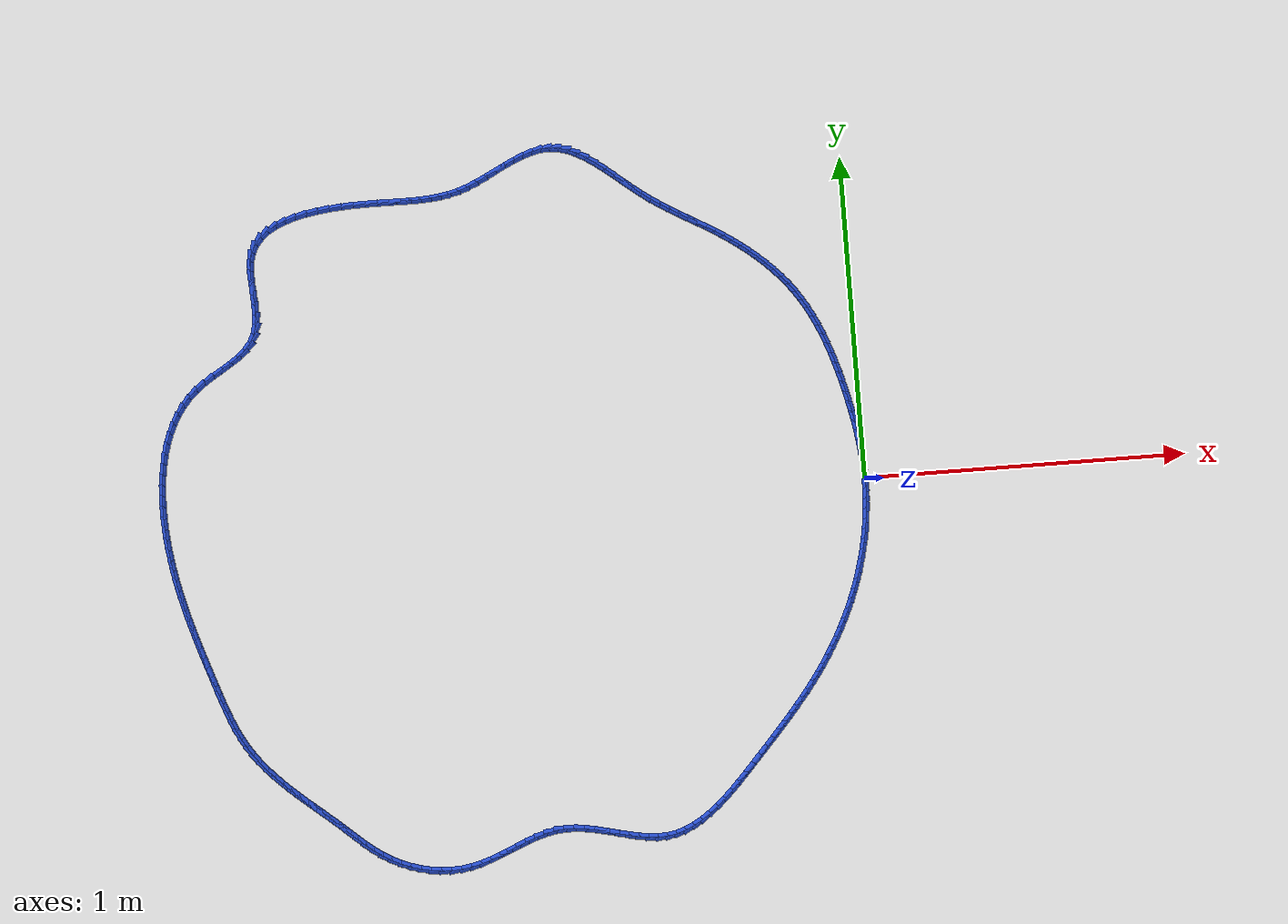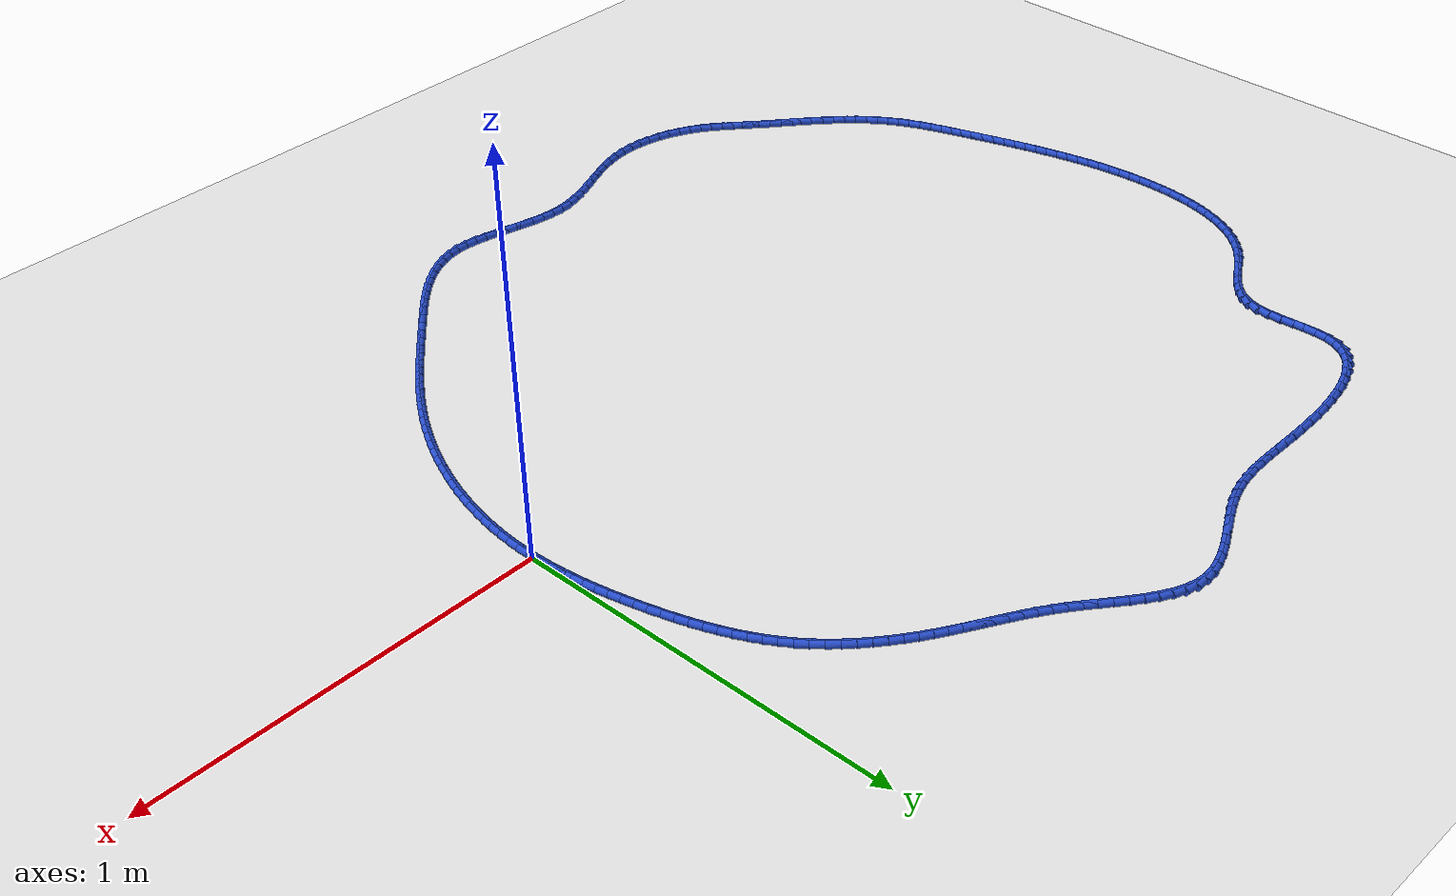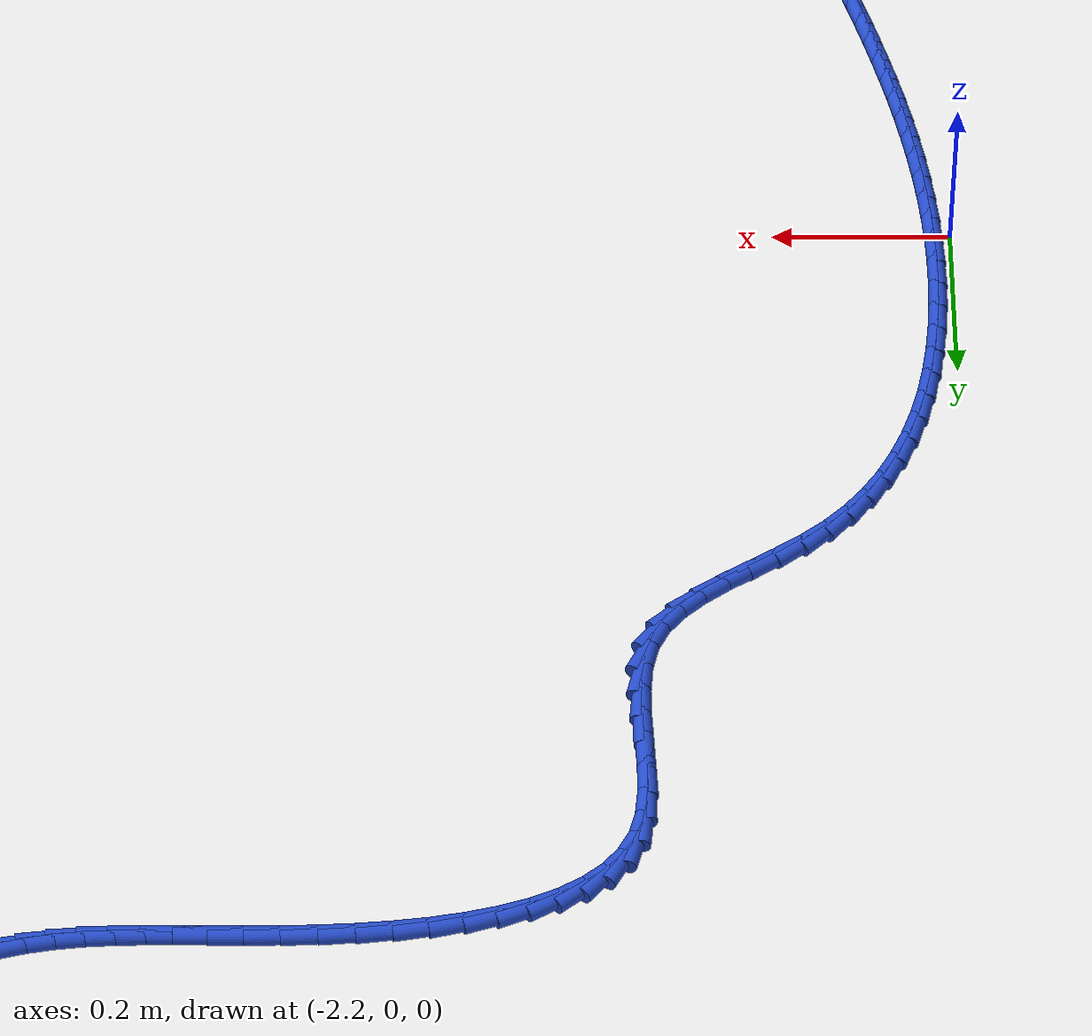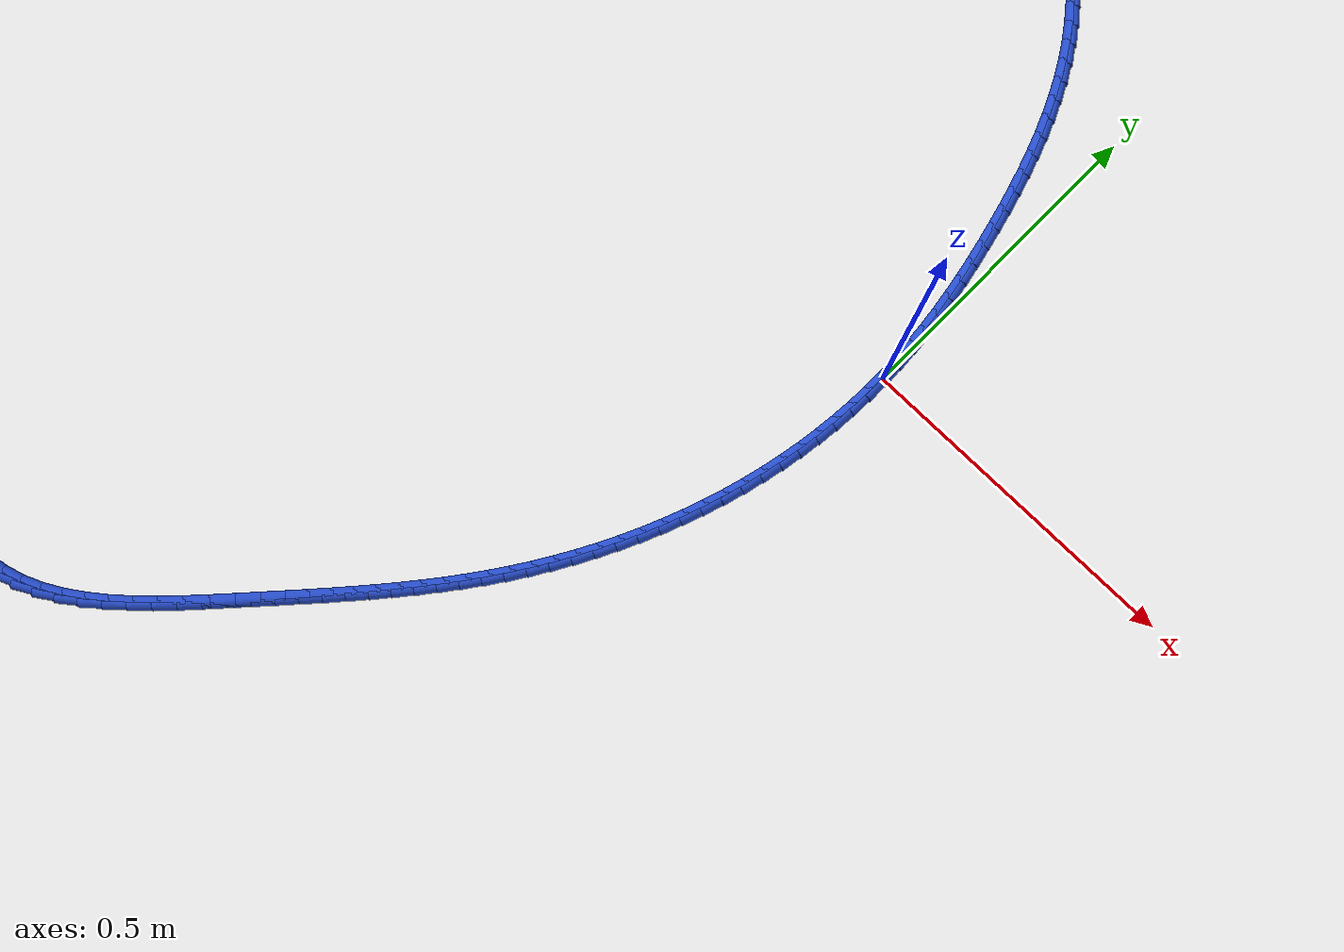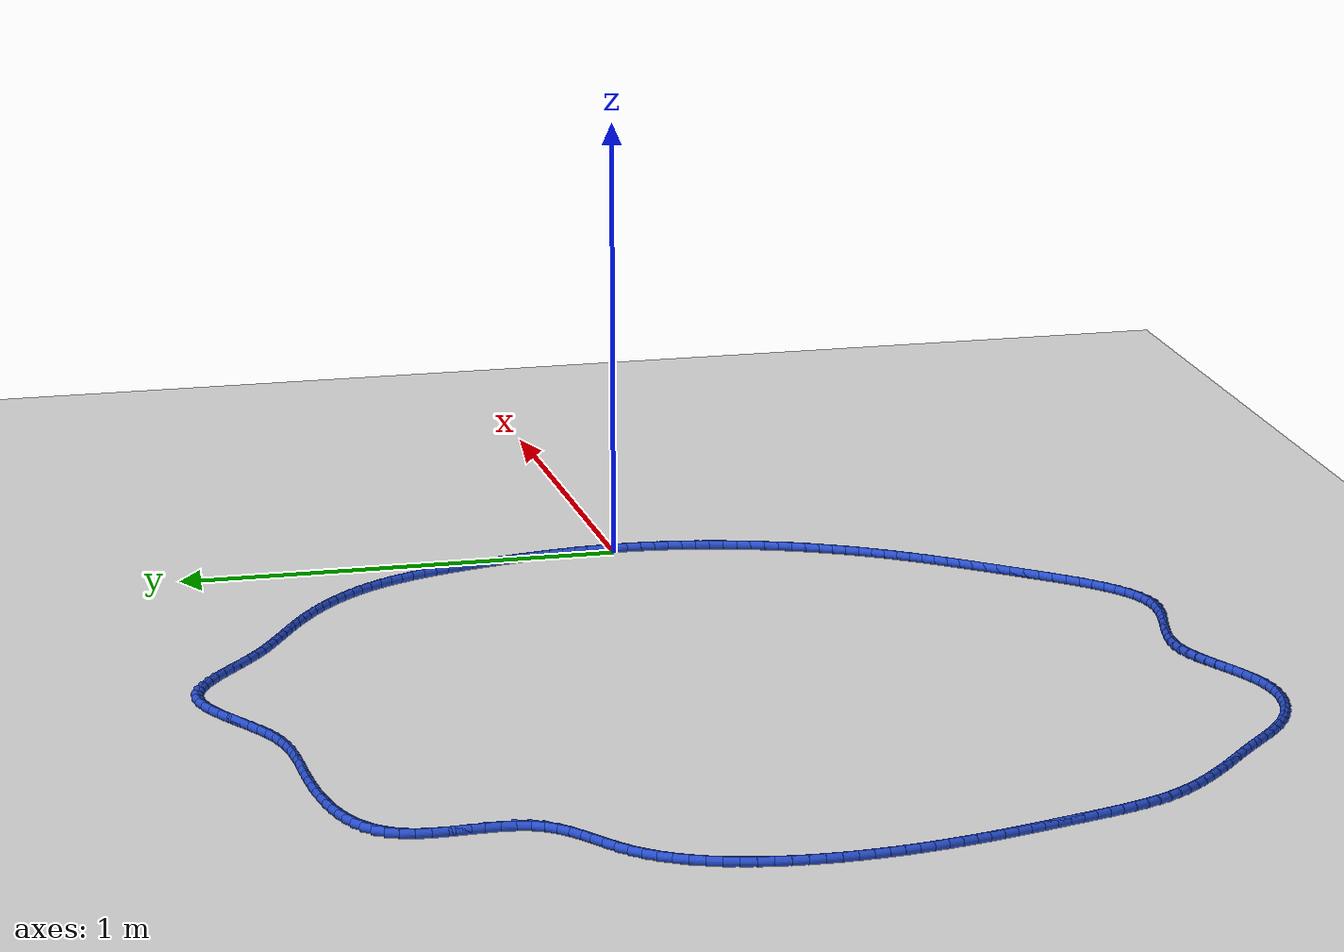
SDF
<sdf version="1.6">
 <world name="default">
  <light name="sun" type="directional">
   <pose>0 0 10 0 -0 0</pose>
   <diffuse>0.8 0.8 0.8 1</diffuse>
   <specular>0.2 0.2 0.2 1</specular>
   <attenuation>
    <range>1000</range>
    <constant>0.9</constant>
    <linear>0.01</linear>
    <quadratic>0.001</quadratic>
   </attenuation>
   <direction>-0.5 0.1 -0.9</direction>
  </light>
  <model name="ground_plane">
   <static>1</static>
   <link name="link">
    <collision name="collision">
     <geometry><plane><normal>0 0 1</normal><size>100 100</size></plane></geometry>
     <surface><friction><ode><mu>100</mu><mu2>50</mu2></ode></friction></surface>
    </collision>
    <visual name="visual">
     <cast_shadows>0</cast_shadows>
     <geometry><plane><normal>0 0 1</normal><size>100 100</size></plane></geometry>
     <material>
      <script><uri>file://media/materials/scripts/gazebo.material</uri><name>Gazebo/WhiteGlow</name></script>
     </material>
    </visual>
   </link>
  </model>
  <gravity>0 0 -9.8</gravity>
  <magnetic_field>6e-06 2.3e-05 -4.2e-05</magnetic_field>
  <atmosphere type="adiabatic"/>
  <physics name="default_physics" default="0" type="ode">
   <max_step_size>0.001</max_step_size>
   <real_time_factor>1</real_time_factor>
   <real_time_update_rate>1000</real_time_update_rate>
  </physics>
  <scene><ambient>0.4 0.4 0.4 1</ambient><background>0.7 0.7 0.7 1</background><shadows>1</shadows></scene>
  <spherical_coordinates>
   <surface_model>EARTH_WGS84</surface_model>
   <latitude_deg>0</latitude_deg>
   <longitude_deg>0</longitude_deg>
   <elevation>0</elevation>
   <heading_deg>0</heading_deg>
  </spherical_coordinates>
  <model name="line">
   <link name="link_0">
    <pose>4.336808689942018e-18 3.469446951953614e-17 0.01 0 1.57 -1.5415884488783602</pose>
    <collision name="collision">
     <geometry><cylinder><radius>0.01</radius><length>0.08</length></cylinder></geometry>
    </collision>
    <visual name="visual">
     <material>
      <script><name>Gazebo/Blue</name><uri>file://media/materials/scripts/gazebo.material</uri></script>
     </material>
     <geometry><cylinder><radius>0.01</radius><length>0.08</length></cylinder></geometry>
    </visual>
   </link>
   <link name="link_1">
    <pose>-0.0009183013230216314 0.031431252091147034 0.01 0 1.57 -1.5081474570677618</pose>
    <collision name="collision">
     <geometry><cylinder><radius>0.01</radius><length>0.08</length></cylinder></geometry>
    </collision>
    <visual name="visual">
     <material>
      <script><name>Gazebo/Blue</name><uri>file://media/materials/scripts/gazebo.material</uri></script>
     </material>
     <geometry><cylinder><radius>0.01</radius><length>0.08</length></cylinder></geometry>
    </visual>
   </link>
   <link name="link_2">
    <pose>-0.0028864127806761068 0.06280509689555297 0.01 0 1.57 -1.4768871577441558</pose>
    <collision name="collision">
     <geometry><cylinder><radius>0.01</radius><length>0.08</length></cylinder></geometry>
    </collision>
    <visual name="visual">
     <material>
      <script><name>Gazebo/Blue</name><uri>file://media/materials/scripts/gazebo.material</uri></script>
     </material>
     <geometry><cylinder><radius>0.01</radius><length>0.08</length></cylinder></geometry>
    </visual>
   </link>
   <link name="link_3">
    <pose>-0.005836260036497518 0.09412440982551427 0.01 0 1.57 -1.4478570005480693</pose>
    <collision name="collision">
     <geometry><cylinder><radius>0.01</radius><length>0.08</length></cylinder></geometry>
    </collision>
    <visual name="visual">
     <material>
      <script><name>Gazebo/Blue</name><uri>file://media/materials/scripts/gazebo.material</uri></script>
     </material>
     <geometry><cylinder><radius>0.01</radius><length>0.08</length></cylinder></geometry>
    </visual>
   </link>
   <link name="link_4">
    <pose>-0.009699768754019965 0.12539206629332744 0.01 0 1.57 -1.4210836907950506</pose>
    <collision name="collision">
     <geometry><cylinder><radius>0.01</radius><length>0.08</length></cylinder></geometry>
    </collision>
    <visual name="visual">
     <material>
      <script><name>Gazebo/Blue</name><uri>file://media/materials/scripts/gazebo.material</uri></script>
     </material>
     <geometry><cylinder><radius>0.01</radius><length>0.08</length></cylinder></geometry>
    </visual>
   </link>
   <link name="link_5">
    <pose>-0.014408864596777551 0.156610941711289 0.01 0 1.57 -1.3965753767757954</pose>
    <collision name="collision">
     <geometry><cylinder><radius>0.01</radius><length>0.08</length></cylinder></geometry>
    </collision>
    <visual name="visual">
     <material>
      <script><name>Gazebo/Blue</name><uri>file://media/materials/scripts/gazebo.material</uri></script>
     </material>
     <geometry><cylinder><radius>0.01</radius><length>0.08</length></cylinder></geometry>
    </visual>
   </link>
   <link name="link_6">
    <pose>-0.019895473228304372 0.1877839114916954 0.01 0 1.57 -1.3743257470452452</pose>
    <collision name="collision">
     <geometry><cylinder><radius>0.01</radius><length>0.08</length></cylinder></geometry>
    </collision>
    <visual name="visual">
     <material>
      <script><name>Gazebo/Blue</name><uri>file://media/materials/scripts/gazebo.material</uri></script>
     </material>
     <geometry><cylinder><radius>0.01</radius><length>0.08</length></cylinder></geometry>
    </visual>
   </link>
   <link name="link_7">
    <pose>-0.026091520312134533 0.21891385104684313 0.01 0 1.57 -1.3543178584303566</pose>
    <collision name="collision">
     <geometry><cylinder><radius>0.01</radius><length>0.08</length></cylinder></geometry>
    </collision>
    <visual name="visual">
     <material>
      <script><name>Gazebo/Blue</name><uri>file://media/materials/scripts/gazebo.material</uri></script>
     </material>
     <geometry><cylinder><radius>0.01</radius><length>0.08</length></cylinder></geometry>
    </visual>
   </link>
   <link name="link_8">
    <pose>-0.032928931511802144 0.25000363578902873 0.01 0 1.57 -1.3365275845765345</pose>
    <collision name="collision">
     <geometry><cylinder><radius>0.01</radius><length>0.08</length></cylinder></geometry>
    </collision>
    <visual name="visual">
     <material>
      <script><name>Gazebo/Blue</name><uri>file://media/materials/scripts/gazebo.material</uri></script>
     </material>
     <geometry><cylinder><radius>0.01</radius><length>0.08</length></cylinder></geometry>
    </visual>
   </link>
   <link name="link_9">
    <pose>-0.04033963249084128 0.28105614113054855 0.01 0 1.57 -1.3200836614919882</pose>
    <collision name="collision">
     <geometry><cylinder><radius>0.01</radius><length>0.08</length></cylinder></geometry>
    </collision>
    <visual name="visual">
     <material>
      <script><name>Gazebo/Blue</name><uri>file://media/materials/scripts/gazebo.material</uri></script>
     </material>
     <geometry><cylinder><radius>0.01</radius><length>0.08</length></cylinder></geometry>
    </visual>
   </link>
   <link name="link_10">
    <pose>-0.04827984922859303 0.31206035759031553 0.01 0 1.57 -1.3013412949501342</pose>
    <collision name="collision">
     <geometry><cylinder><radius>0.01</radius><length>0.08</length></cylinder></geometry>
    </collision>
    <visual name="visual">
     <material>
      <script><name>Gazebo/Blue</name><uri>file://media/materials/scripts/gazebo.material</uri></script>
     </material>
     <geometry><cylinder><radius>0.01</radius><length>0.08</length></cylinder></geometry>
    </visual>
   </link>
   <link name="link_11">
    <pose>-0.05680957892490114 0.3429459821231411 0.01 0 1.57 -1.2792599001472036</pose>
    <collision name="collision">
     <geometry><cylinder><radius>0.01</radius><length>0.08</length></cylinder></geometry>
    </collision>
    <visual name="visual">
     <material>
      <script><name>Gazebo/Blue</name><uri>file://media/materials/scripts/gazebo.material</uri></script>
     </material>
     <geometry><cylinder><radius>0.01</radius><length>0.08</length></cylinder></geometry>
    </visual>
   </link>
   <link name="link_12">
    <pose>-0.06601651359103096 0.3736268872185536 0.01 0 1.57 -1.2537377770622167</pose>
    <collision name="collision">
     <geometry><cylinder><radius>0.01</radius><length>0.08</length></cylinder></geometry>
    </collision>
    <visual name="visual">
     <material>
      <script><name>Gazebo/Blue</name><uri>file://media/materials/scripts/gazebo.material</uri></script>
     </material>
     <geometry><cylinder><radius>0.01</radius><length>0.08</length></cylinder></geometry>
    </visual>
   </link>
   <link name="link_13">
    <pose>-0.07598834550704953 0.4040169452124909 0.01 0 1.57 -1.2246594559088175</pose>
    <collision name="collision">
     <geometry><cylinder><radius>0.01</radius><length>0.08</length></cylinder></geometry>
    </collision>
    <visual name="visual">
     <material>
      <script><name>Gazebo/Blue</name><uri>file://media/materials/scripts/gazebo.material</uri></script>
     </material>
     <geometry><cylinder><radius>0.01</radius><length>0.08</length></cylinder></geometry>
    </visual>
   </link>
   <link name="link_14">
    <pose>-0.08681276695302381 0.4340300284408909 0.01 0 1.57 -1.1919039512613172</pose>
    <collision name="collision">
     <geometry><cylinder><radius>0.01</radius><length>0.08</length></cylinder></geometry>
    </collision>
    <visual name="visual">
     <material>
      <script><name>Gazebo/Blue</name><uri>file://media/materials/scripts/gazebo.material</uri></script>
     </material>
     <geometry><cylinder><radius>0.01</radius><length>0.08</length></cylinder></geometry>
    </visual>
   </link>
   <link name="link_15">
    <pose>-0.0985774702090209 0.463580009239692 0.01 0 1.57 -1.1553553642338417</pose>
    <collision name="collision">
     <geometry><cylinder><radius>0.01</radius><length>0.08</length></cylinder></geometry>
    </collision>
    <visual name="visual">
     <material>
      <script><name>Gazebo/Blue</name><uri>file://media/materials/scripts/gazebo.material</uri></script>
     </material>
     <geometry><cylinder><radius>0.01</radius><length>0.08</length></cylinder></geometry>
    </visual>
   </link>
   <link name="link_16">
    <pose>-0.11137014755510781 0.492580759944832 0.01 0 1.57 -1.1149162891457438</pose>
    <collision name="collision">
     <geometry><cylinder><radius>0.01</radius><length>0.08</length></cylinder></geometry>
    </collision>
    <visual name="visual">
     <material>
      <script><name>Gazebo/Blue</name><uri>file://media/materials/scripts/gazebo.material</uri></script>
     </material>
     <geometry><cylinder><radius>0.01</radius><length>0.08</length></cylinder></geometry>
    </visual>
   </link>
   <link name="link_17">
    <pose>-0.12527849127135163 0.5209461528922493 0.01 0 1.57 -1.070524265495265</pose>
    <collision name="collision">
     <geometry><cylinder><radius>0.01</radius><length>0.08</length></cylinder></geometry>
    </collision>
    <visual name="visual">
     <material>
      <script><name>Gazebo/Blue</name><uri>file://media/materials/scripts/gazebo.material</uri></script>
     </material>
     <geometry><cylinder><radius>0.01</radius><length>0.08</length></cylinder></geometry>
    </visual>
   </link>
   <link name="link_18">
    <pose>-0.14039019363781932 0.5485900604178819 0.01 0 1.57 -1.0221710814675207</pose>
    <collision name="collision">
     <geometry><cylinder><radius>0.01</radius><length>0.08</length></cylinder></geometry>
    </collision>
    <visual name="visual">
     <material>
      <script><name>Gazebo/Blue</name><uri>file://media/materials/scripts/gazebo.material</uri></script>
     </material>
     <geometry><cylinder><radius>0.01</radius><length>0.08</length></cylinder></geometry>
    </visual>
   </link>
   <link name="link_19">
    <pose>-0.1567929469345779 0.5754263548576675 0.01 0 1.57 -0.9699240420496735</pose>
    <collision name="collision">
     <geometry><cylinder><radius>0.01</radius><length>0.08</length></cylinder></geometry>
    </collision>
    <visual name="visual">
     <material>
      <script><name>Gazebo/Blue</name><uri>file://media/materials/scripts/gazebo.material</uri></script>
     </material>
     <geometry><cylinder><radius>0.01</radius><length>0.08</length></cylinder></geometry>
    </visual>
   </link>
   <link name="link_20">
    <pose>-0.1745744434416945 0.6013689085475447 0.01 0 1.57 -0.9144297529021951</pose>
    <collision name="collision">
     <geometry><cylinder><radius>0.01</radius><length>0.08</length></cylinder></geometry>
    </collision>
    <visual name="visual">
     <material>
      <script><name>Gazebo/Blue</name><uri>file://media/materials/scripts/gazebo.material</uri></script>
     </material>
     <geometry><cylinder><radius>0.01</radius><length>0.08</length></cylinder></geometry>
    </visual>
   </link>
   <link name="link_21">
    <pose>-0.1938078844427915 0.6263376986353224 0.01 0 1.57 -0.8604891405685786</pose>
    <collision name="collision">
     <geometry><cylinder><radius>0.01</radius><length>0.08</length></cylinder></geometry>
    </collision>
    <visual name="visual">
     <material>
      <script><name>Gazebo/Blue</name><uri>file://media/materials/scripts/gazebo.material</uri></script>
     </material>
     <geometry><cylinder><radius>0.01</radius><length>0.08</length></cylinder></geometry>
    </visual>
   </link>
   <link name="link_22">
    <pose>-0.2144268732661305 0.6503115125278844 0.01 0 1.57 -0.8105958679355366</pose>
    <collision name="collision">
     <geometry><cylinder><radius>0.01</radius><length>0.08</length></cylinder></geometry>
    </collision>
    <visual name="visual">
     <material>
      <script><name>Gazebo/Blue</name><uri>file://media/materials/scripts/gazebo.material</uri></script>
     </material>
     <geometry><cylinder><radius>0.01</radius><length>0.08</length></cylinder></geometry>
    </visual>
   </link>
   <link name="link_23">
    <pose>-0.2362869945524651 0.6733020055864684 0.01 0 1.57 -0.764571923039052</pose>
    <collision name="collision">
     <geometry><cylinder><radius>0.01</radius><length>0.08</length></cylinder></geometry>
    </collision>
    <visual name="visual">
     <material>
      <script><name>Gazebo/Blue</name><uri>file://media/materials/scripts/gazebo.material</uri></script>
     </material>
     <geometry><cylinder><radius>0.01</radius><length>0.08</length></cylinder></geometry>
    </visual>
   </link>
   <link name="link_24">
    <pose>-0.25924298046999433 0.6953211923045908 0.01 0 1.57 -0.7221756437003981</pose>
    <collision name="collision">
     <geometry><cylinder><radius>0.01</radius><length>0.08</length></cylinder></geometry>
    </collision>
    <visual name="visual">
     <material>
      <script><name>Gazebo/Blue</name><uri>file://media/materials/scripts/gazebo.material</uri></script>
     </material>
     <geometry><cylinder><radius>0.01</radius><length>0.08</length></cylinder></geometry>
    </visual>
   </link>
   <link name="link_25">
    <pose>-0.2831495631869171 0.7163810871757685 0.01 0 1.57 -0.6831493544724059</pose>
    <collision name="collision">
     <geometry><cylinder><radius>0.01</radius><length>0.08</length></cylinder></geometry>
    </collision>
    <visual name="visual">
     <material>
      <script><name>Gazebo/Blue</name><uri>file://media/materials/scripts/gazebo.material</uri></script>
     </material>
     <geometry><cylinder><radius>0.01</radius><length>0.08</length></cylinder></geometry>
    </visual>
   </link>
   <link name="link_26">
    <pose>-0.30786147487143245 0.736493704693518 0.01 0 1.57 -0.6472333285248579</pose>
    <collision name="collision">
     <geometry><cylinder><radius>0.01</radius><length>0.08</length></cylinder></geometry>
    </collision>
    <visual name="visual">
     <material>
      <script><name>Gazebo/Blue</name><uri>file://media/materials/scripts/gazebo.material</uri></script>
     </material>
     <geometry><cylinder><radius>0.01</radius><length>0.08</length></cylinder></geometry>
    </visual>
   </link>
   <link name="link_27">
    <pose>-0.33323344769173946 0.7556710593513561 0.01 0 1.57 -0.6141753557104128</pose>
    <collision name="collision">
     <geometry><cylinder><radius>0.01</radius><length>0.08</length></cylinder></geometry>
    </collision>
    <visual name="visual">
     <material>
      <script><name>Gazebo/Blue</name><uri>file://media/materials/scripts/gazebo.material</uri></script>
     </material>
     <geometry><cylinder><radius>0.01</radius><length>0.08</length></cylinder></geometry>
    </visual>
   </link>
   <link name="link_28">
    <pose>-0.359120213816037 0.7739251656427995 0.01 0 1.57 -0.5837369270911804</pose>
    <collision name="collision">
     <geometry><cylinder><radius>0.01</radius><length>0.08</length></cylinder></geometry>
    </collision>
    <visual name="visual">
     <material>
      <script><name>Gazebo/Blue</name><uri>file://media/materials/scripts/gazebo.material</uri></script>
     </material>
     <geometry><cylinder><radius>0.01</radius><length>0.08</length></cylinder></geometry>
    </visual>
   </link>
   <link name="link_29">
    <pose>-0.38537650583038136 0.791268039102548 0.01 0 1.57 -0.5566629691196182</pose>
    <collision name="collision">
     <geometry><cylinder><radius>0.01</radius><length>0.08</length></cylinder></geometry>
    </collision>
    <visual name="visual">
     <material>
      <script><name>Gazebo/Blue</name><uri>file://media/materials/scripts/gazebo.material</uri></script>
     </material>
     <geometry><cylinder><radius>0.01</radius><length>0.08</length></cylinder></geometry>
    </visual>
   </link>
   <link name="link_30">
    <pose>-0.4118760296805622 0.8077589715701352 0.01 0 1.57 -0.5365555119013853</pose>
    <collision name="collision">
     <geometry><cylinder><radius>0.01</radius><length>0.08</length></cylinder></geometry>
    </collision>
    <visual name="visual">
     <material>
      <script><name>Gazebo/Blue</name><uri>file://media/materials/scripts/gazebo.material</uri></script>
     </material>
     <geometry><cylinder><radius>0.01</radius><length>0.08</length></cylinder></geometry>
    </visual>
   </link>
   <link name="link_31">
    <pose>-0.43856210064839085 0.8236307018778918 0.01 0 1.57 -0.5245383648477828</pose>
    <collision name="collision">
     <geometry><cylinder><radius>0.01</radius><length>0.08</length></cylinder></geometry>
    </collision>
    <visual name="visual">
     <material>
      <script><name>Gazebo/Blue</name><uri>file://media/materials/scripts/gazebo.material</uri></script>
     </material>
     <geometry><cylinder><radius>0.01</radius><length>0.08</length></cylinder></geometry>
    </visual>
   </link>
   <link name="link_32">
    <pose>-0.46539399343498583 0.8391557352665624 0.01 0 1.57 -0.5207754905481475</pose>
    <collision name="collision">
     <geometry><cylinder><radius>0.01</radius><length>0.08</length></cylinder></geometry>
    </collision>
    <visual name="visual">
     <material>
      <script><name>Gazebo/Blue</name><uri>file://media/materials/scripts/gazebo.material</uri></script>
     </material>
     <geometry><cylinder><radius>0.01</radius><length>0.08</length></cylinder></geometry>
    </visual>
   </link>
   <link name="link_33">
    <pose>-0.4923309827414663 0.8546065769768924 0.01 0 1.57 -0.5252613290431674</pose>
    <collision name="collision">
     <geometry><cylinder><radius>0.01</radius><length>0.08</length></cylinder></geometry>
    </collision>
    <visual name="visual">
     <material>
      <script><name>Gazebo/Blue</name><uri>file://media/materials/scripts/gazebo.material</uri></script>
     </material>
     <geometry><cylinder><radius>0.01</radius><length>0.08</length></cylinder></geometry>
    </visual>
   </link>
   <link name="link_34">
    <pose>-0.5193323432689506 0.8702557322496259 0.01 0 1.57 -0.5378299260536323</pose>
    <collision name="collision">
     <geometry><cylinder><radius>0.01</radius><length>0.08</length></cylinder></geometry>
    </collision>
    <visual name="visual">
     <material>
      <script><name>Gazebo/Blue</name><uri>file://media/materials/scripts/gazebo.material</uri></script>
     </material>
     <geometry><cylinder><radius>0.01</radius><length>0.08</length></cylinder></geometry>
    </visual>
   </link>
   <link name="link_35">
    <pose>-0.5463573497185578 0.8863757063255084 0.01 0 1.57 -0.5581557091165403</pose>
    <collision name="collision">
     <geometry><cylinder><radius>0.01</radius><length>0.08</length></cylinder></geometry>
    </collision>
    <visual name="visual">
     <material>
      <script><name>Gazebo/Blue</name><uri>file://media/materials/scripts/gazebo.material</uri></script>
     </material>
     <geometry><cylinder><radius>0.01</radius><length>0.08</length></cylinder></geometry>
    </visual>
   </link>
   <link name="link_36">
    <pose>-0.5733652767914065 0.903239004445284 0.01 0 1.57 -0.5857483779901602</pose>
    <collision name="collision">
     <geometry><cylinder><radius>0.01</radius><length>0.08</length></cylinder></geometry>
    </collision>
    <visual name="visual">
     <material>
      <script><name>Gazebo/Blue</name><uri>file://media/materials/scripts/gazebo.material</uri></script>
     </material>
     <geometry><cylinder><radius>0.01</radius><length>0.08</length></cylinder></geometry>
    </visual>
   </link>
   <link name="link_37">
    <pose>-0.6003153991886154 0.921118131849698 0.01 0 1.57 -0.6199470423123975</pose>
    <collision name="collision">
     <geometry><cylinder><radius>0.01</radius><length>0.08</length></cylinder></geometry>
    </collision>
    <visual name="visual">
     <material>
      <script><name>Gazebo/Blue</name><uri>file://media/materials/scripts/gazebo.material</uri></script>
     </material>
     <geometry><cylinder><radius>0.01</radius><length>0.08</length></cylinder></geometry>
    </visual>
   </link>
   <link name="link_38">
    <pose>-0.6271669930591545 0.9402855798955739 0.01 0 1.57 -0.6552976232309352</pose>
    <collision name="collision">
     <geometry><cylinder><radius>0.01</radius><length>0.08</length></cylinder></geometry>
    </collision>
    <visual name="visual">
     <material>
      <script><name>Gazebo/Blue</name><uri>file://media/materials/scripts/gazebo.material</uri></script>
     </material>
     <geometry><cylinder><radius>0.01</radius><length>0.08</length></cylinder></geometry>
    </visual>
   </link>
   <link name="link_39">
    <pose>-0.6538983752682669 0.9608312522392101 0.01 0 1.57 -0.6758624609758725</pose>
    <collision name="collision">
     <geometry><cylinder><radius>0.01</radius><length>0.08</length></cylinder></geometry>
    </collision>
    <visual name="visual">
     <material>
      <script><name>Gazebo/Blue</name><uri>file://media/materials/scripts/gazebo.material</uri></script>
     </material>
     <geometry><cylinder><radius>0.01</radius><length>0.08</length></cylinder></geometry>
    </visual>
   </link>
   <link name="link_40">
    <pose>-0.6805545789996227 0.9822052877825593 0.01 0 1.57 -0.6793010369439788</pose>
    <collision name="collision">
     <geometry><cylinder><radius>0.01</radius><length>0.08</length></cylinder></geometry>
    </collision>
    <visual name="visual">
     <material>
      <script><name>Gazebo/Blue</name><uri>file://media/materials/scripts/gazebo.material</uri></script>
     </material>
     <geometry><cylinder><radius>0.01</radius><length>0.08</length></cylinder></geometry>
    </visual>
   </link>
   <link name="link_41">
    <pose>-0.7071952414934762 1.0037177823182872 0.01 0 1.57 -0.665840706513501</pose>
    <collision name="collision">
     <geometry><cylinder><radius>0.01</radius><length>0.08</length></cylinder></geometry>
    </collision>
    <visual name="visual">
     <material>
      <script><name>Gazebo/Blue</name><uri>file://media/materials/scripts/gazebo.material</uri></script>
     </material>
     <geometry><cylinder><radius>0.01</radius><length>0.08</length></cylinder></geometry>
    </visual>
   </link>
   <link name="link_42">
    <pose>-0.7338799999900811 1.0246788316390563 0.01 0 1.57 -0.6345623281032866</pose>
    <collision name="collision">
     <geometry><cylinder><radius>0.01</radius><length>0.08</length></cylinder></geometry>
    </collision>
    <visual name="visual">
     <material>
      <script><name>Gazebo/Blue</name><uri>file://media/materials/scripts/gazebo.material</uri></script>
     </material>
     <geometry><cylinder><radius>0.01</radius><length>0.08</length></cylinder></geometry>
    </visual>
   </link>
   <link name="link_43">
    <pose>-0.7606684917296919 1.0443985315375317 0.01 0 1.57 -0.5833786205682988</pose>
    <collision name="collision">
     <geometry><cylinder><radius>0.01</radius><length>0.08</length></cylinder></geometry>
    </collision>
    <visual name="visual">
     <material>
      <script><name>Gazebo/Blue</name><uri>file://media/materials/scripts/gazebo.material</uri></script>
     </material>
     <geometry><cylinder><radius>0.01</radius><length>0.08</length></cylinder></geometry>
    </visual>
   </link>
   <link name="link_44">
    <pose>-0.7876203539525625 1.0621869778063777 0.01 0 1.57 -0.5090686201910547</pose>
    <collision name="collision">
     <geometry><cylinder><radius>0.01</radius><length>0.08</length></cylinder></geometry>
    </collision>
    <visual name="visual">
     <material>
      <script><name>Gazebo/Blue</name><uri>file://media/materials/scripts/gazebo.material</uri></script>
     </material>
     <geometry><cylinder><radius>0.01</radius><length>0.08</length></cylinder></geometry>
    </visual>
   </link>
   <link name="link_45">
    <pose>-0.8147952238989468 1.0773542662382578 0.01 0 1.57 -0.4076183742638912</pose>
    <collision name="collision">
     <geometry><cylinder><radius>0.01</radius><length>0.08</length></cylinder></geometry>
    </collision>
    <visual name="visual">
     <material>
      <script><name>Gazebo/Blue</name><uri>file://media/materials/scripts/gazebo.material</uri></script>
     </material>
     <geometry><cylinder><radius>0.01</radius><length>0.08</length></cylinder></geometry>
    </visual>
   </link>
   <link name="link_46">
    <pose>-0.8422527388090992 1.089210492625837 0.01 0 1.57 -0.2753859879252237</pose>
    <collision name="collision">
     <geometry><cylinder><radius>0.01</radius><length>0.08</length></cylinder></geometry>
    </collision>
    <visual name="visual">
     <material>
      <script><name>Gazebo/Blue</name><uri>file://media/materials/scripts/gazebo.material</uri></script>
     </material>
     <geometry><cylinder><radius>0.01</radius><length>0.08</length></cylinder></geometry>
    </visual>
   </link>
   <link name="link_47">
    <pose>-0.8700525359232736 1.0970657527617786 0.01 0 1.57 -0.11174718933897536</pose>
    <collision name="collision">
     <geometry><cylinder><radius>0.01</radius><length>0.08</length></cylinder></geometry>
    </collision>
    <visual name="visual">
     <material>
      <script><name>Gazebo/Blue</name><uri>file://media/materials/scripts/gazebo.material</uri></script>
     </material>
     <geometry><cylinder><radius>0.01</radius><length>0.08</length></cylinder></geometry>
    </visual>
   </link>
   <link name="link_48">
    <pose>-0.8982542319171419 1.1002303967643918 0.01 0 1.57 0.06527431237848366</pose>
    <collision name="collision">
     <geometry><cylinder><radius>0.01</radius><length>0.08</length></cylinder></geometry>
    </collision>
    <visual name="visual">
     <material>
      <script><name>Gazebo/Blue</name><uri>file://media/materials/scripts/gazebo.material</uri></script>
     </material>
     <geometry><cylinder><radius>0.01</radius><length>0.08</length></cylinder></geometry>
    </visual>
   </link>
   <link name="link_49">
    <pose>-0.9268896435680026 1.0983585807659266 0.01 0 1.57 0.21150004284327814</pose>
    <collision name="collision">
     <geometry><cylinder><radius>0.01</radius><length>0.08</length></cylinder></geometry>
    </collision>
    <visual name="visual">
     <material>
      <script><name>Gazebo/Blue</name><uri>file://media/materials/scripts/gazebo.material</uri></script>
     </material>
     <geometry><cylinder><radius>0.01</radius><length>0.08</length></cylinder></geometry>
    </visual>
   </link>
   <link name="link_50">
    <pose>-0.9559078205961535 1.0921280549985666 0.01 0 1.57 0.32002006329100824</pose>
    <collision name="collision">
     <geometry><cylinder><radius>0.01</radius><length>0.08</length></cylinder></geometry>
    </collision>
    <visual name="visual">
     <material>
      <script><name>Gazebo/Blue</name><uri>file://media/materials/scripts/gazebo.material</uri></script>
     </material>
     <geometry><cylinder><radius>0.01</radius><length>0.08</length></cylinder></geometry>
    </visual>
   </link>
   <link name="link_51">
    <pose>-0.985242478800576 1.0824062068757074 0.01 0 1.57 0.3953313053841322</pose>
    <collision name="collision">
     <geometry><cylinder><radius>0.01</radius><length>0.08</length></cylinder></geometry>
    </collision>
    <visual name="visual">
     <material>
      <script><name>Gazebo/Blue</name><uri>file://media/materials/scripts/gazebo.material</uri></script>
     </material>
     <geometry><cylinder><radius>0.01</radius><length>0.08</length></cylinder></geometry>
    </visual>
   </link>
   <link name="link_52">
    <pose>-1.0148273339802523 1.0700604238107445 0.01 0 1.57 0.442410856456447</pose>
    <collision name="collision">
     <geometry><cylinder><radius>0.01</radius><length>0.08</length></cylinder></geometry>
    </collision>
    <visual name="visual">
     <material>
      <script><name>Gazebo/Blue</name><uri>file://media/materials/scripts/gazebo.material</uri></script>
     </material>
     <geometry><cylinder><radius>0.01</radius><length>0.08</length></cylinder></geometry>
    </visual>
   </link>
   <link name="link_53">
    <pose>-1.0445961019341643 1.0559580932170725 0.01 0 1.57 0.46493946698764704</pose>
    <collision name="collision">
     <geometry><cylinder><radius>0.01</radius><length>0.08</length></cylinder></geometry>
    </collision>
    <visual name="visual">
     <material>
      <script><name>Gazebo/Blue</name><uri>file://media/materials/scripts/gazebo.material</uri></script>
     </material>
     <geometry><cylinder><radius>0.01</radius><length>0.08</length></cylinder></geometry>
    </visual>
   </link>
   <link name="link_54">
    <pose>-1.0744824984612946 1.0409666025080873 0.01 0 1.57 0.4648331794176635</pose>
    <collision name="collision">
     <geometry><cylinder><radius>0.01</radius><length>0.08</length></cylinder></geometry>
    </collision>
    <visual name="visual">
     <material>
      <script><name>Gazebo/Blue</name><uri>file://media/materials/scripts/gazebo.material</uri></script>
     </material>
     <geometry><cylinder><radius>0.01</radius><length>0.08</length></cylinder></geometry>
    </visual>
   </link>
   <link name="link_55">
    <pose>-1.1044202393606253 1.0259533390971847 0.01 0 1.57 0.4422019857636951</pose>
    <collision name="collision">
     <geometry><cylinder><radius>0.01</radius><length>0.08</length></cylinder></geometry>
    </collision>
    <visual name="visual">
     <material>
      <script><name>Gazebo/Blue</name><uri>file://media/materials/scripts/gazebo.material</uri></script>
     </material>
     <geometry><cylinder><radius>0.01</radius><length>0.08</length></cylinder></geometry>
    </visual>
   </link>
   <link name="link_56">
    <pose>-1.1343430404311377 1.0117856903977593 0.01 0 1.57 0.39538077260178434</pose>
    <collision name="collision">
     <geometry><cylinder><radius>0.01</radius><length>0.08</length></cylinder></geometry>
    </collision>
    <visual name="visual">
     <material>
      <script><name>Gazebo/Blue</name><uri>file://media/materials/scripts/gazebo.material</uri></script>
     </material>
     <geometry><cylinder><radius>0.01</radius><length>0.08</length></cylinder></geometry>
    </visual>
   </link>
   <link name="link_57">
    <pose>-1.1641846174718147 0.9993310438232068 0.01 0 1.57 0.322494322950489</pose>
    <collision name="collision">
     <geometry><cylinder><radius>0.01</radius><length>0.08</length></cylinder></geometry>
    </collision>
    <visual name="visual">
     <material>
      <script><name>Gazebo/Blue</name><uri>file://media/materials/scripts/gazebo.material</uri></script>
     </material>
     <geometry><cylinder><radius>0.01</radius><length>0.08</length></cylinder></geometry>
    </visual>
   </link>
   <link name="link_58">
    <pose>-1.1938896981670368 0.9894047956049336 0.01 0 1.57 0.24072029225264766</pose>
    <collision name="collision">
     <geometry><cylinder><radius>0.01</radius><length>0.08</length></cylinder></geometry>
    </collision>
    <visual name="visual">
     <material>
      <script><name>Gazebo/Blue</name><uri>file://media/materials/scripts/gazebo.material</uri></script>
     </material>
     <geometry><cylinder><radius>0.01</radius><length>0.08</length></cylinder></geometry>
    </visual>
   </link>
   <link name="link_59">
    <pose>-1.2235510214620184 0.9821235260932467 0.01 0 1.57 0.16679579527315663</pose>
    <collision name="collision">
     <geometry><cylinder><radius>0.01</radius><length>0.08</length></cylinder></geometry>
    </collision>
    <visual name="visual">
     <material>
      <script><name>Gazebo/Blue</name><uri>file://media/materials/scripts/gazebo.material</uri></script>
     </material>
     <geometry><cylinder><radius>0.01</radius><length>0.08</length></cylinder></geometry>
    </visual>
   </link>
   <link name="link_60">
    <pose>-1.2533672598767625 0.9771036640689655 0.01 0 1.57 0.10411874694446065</pose>
    <collision name="collision">
     <geometry><cylinder><radius>0.01</radius><length>0.08</length></cylinder></geometry>
    </collision>
    <visual name="visual">
     <material>
      <script><name>Gazebo/Blue</name><uri>file://media/materials/scripts/gazebo.material</uri></script>
     </material>
     <geometry><cylinder><radius>0.01</radius><length>0.08</length></cylinder></geometry>
    </visual>
   </link>
   <link name="link_61">
    <pose>-1.2835393860329154 0.9739507786827291 0.01 0 1.57 0.05462815229645936</pose>
    <collision name="collision">
     <geometry><cylinder><radius>0.01</radius><length>0.08</length></cylinder></geometry>
    </collision>
    <visual name="visual">
     <material>
      <script><name>Gazebo/Blue</name><uri>file://media/materials/scripts/gazebo.material</uri></script>
     </material>
     <geometry><cylinder><radius>0.01</radius><length>0.08</length></cylinder></geometry>
    </visual>
   </link>
   <link name="link_62">
    <pose>-1.3142683725521218 0.9722704390851763 0.01 0 1.57 0.019123914383947265</pose>
    <collision name="collision">
     <geometry><cylinder><radius>0.01</radius><length>0.08</length></cylinder></geometry>
    </collision>
    <visual name="visual">
     <material>
      <script><name>Gazebo/Blue</name><uri>file://media/materials/scripts/gazebo.material</uri></script>
     </material>
     <geometry><cylinder><radius>0.01</radius><length>0.08</length></cylinder></geometry>
    </visual>
   </link>
   <link name="link_63">
    <pose>-1.345755192056029 0.9716682144269467 0.01 0 1.57 -0.0025106392711121213</pose>
    <collision name="collision">
     <geometry><cylinder><radius>0.01</radius><length>0.08</length></cylinder></geometry>
    </collision>
    <visual name="visual">
     <material>
      <script><name>Gazebo/Blue</name><uri>file://media/materials/scripts/gazebo.material</uri></script>
     </material>
     <geometry><cylinder><radius>0.01</radius><length>0.08</length></cylinder></geometry>
    </visual>
   </link>
   <link name="link_64">
    <pose>-1.3782008171662805 0.971749673858679 0.01 0 1.57 -0.011030893820782851</pose>
    <collision name="collision">
     <geometry><cylinder><radius>0.01</radius><length>0.08</length></cylinder></geometry>
    </collision>
    <visual name="visual">
     <material>
      <script><name>Gazebo/Blue</name><uri>file://media/materials/scripts/gazebo.material</uri></script>
     </material>
     <geometry><cylinder><radius>0.01</radius><length>0.08</length></cylinder></geometry>
    </visual>
   </link>
   <link name="link_65">
    <pose>-1.4118062205045232 0.9721203865310122 0.01 0 1.57 -0.007594201885368539</pose>
    <collision name="collision">
     <geometry><cylinder><radius>0.01</radius><length>0.08</length></cylinder></geometry>
    </collision>
    <visual name="visual">
     <material>
      <script><name>Gazebo/Blue</name><uri>file://media/materials/scripts/gazebo.material</uri></script>
     </material>
     <geometry><cylinder><radius>0.01</radius><length>0.08</length></cylinder></geometry>
    </visual>
   </link>
   <link name="link_66">
    <pose>-1.4467723311654537 0.9723859313393618 0.01 0 1.57 0.005509216090601147</pose>
    <collision name="collision">
     <geometry><cylinder><radius>0.01</radius><length>0.08</length></cylinder></geometry>
    </collision>
    <visual name="visual">
     <material>
      <script><name>Gazebo/Blue</name><uri>file://media/materials/scripts/gazebo.material</uri></script>
     </material>
     <geometry><cylinder><radius>0.01</radius><length>0.08</length></cylinder></geometry>
    </visual>
   </link>
   <link name="link_67">
    <pose>-1.4831498612118819 0.9721855176378733 0.01 0 1.57 0.02457863378522473</pose>
    <collision name="collision">
     <geometry><cylinder><radius>0.01</radius><length>0.08</length></cylinder></geometry>
    </collision>
    <visual name="visual">
     <material>
      <script><name>Gazebo/Blue</name><uri>file://media/materials/scripts/gazebo.material</uri></script>
     </material>
     <geometry><cylinder><radius>0.01</radius><length>0.08</length></cylinder></geometry>
    </visual>
   </link>
   <link name="link_68">
    <pose>-1.5205031679074472 0.9712672394710468 0.01 0 1.57 0.04933268261214507</pose>
    <collision name="collision">
     <geometry><cylinder><radius>0.01</radius><length>0.08</length></cylinder></geometry>
    </collision>
    <visual name="visual">
     <material>
      <script><name>Gazebo/Blue</name><uri>file://media/materials/scripts/gazebo.material</uri></script>
     </material>
     <geometry><cylinder><radius>0.01</radius><length>0.08</length></cylinder></geometry>
    </visual>
   </link>
   <link name="link_69">
    <pose>-1.5582983570113862 0.9694011873449173 0.01 0 1.57 0.08055419651748409</pose>
    <collision name="collision">
     <geometry><cylinder><radius>0.01</radius><length>0.08</length></cylinder></geometry>
    </collision>
    <visual name="visual">
     <material>
      <script><name>Gazebo/Blue</name><uri>file://media/materials/scripts/gazebo.material</uri></script>
     </material>
     <geometry><cylinder><radius>0.01</radius><length>0.08</length></cylinder></geometry>
    </visual>
   </link>
   <link name="link_70">
    <pose>-1.5960015342829392 0.9663574517655208 0.01 0 1.57 0.11948358979428807</pose>
    <collision name="collision">
     <geometry><cylinder><radius>0.01</radius><length>0.08</length></cylinder></geometry>
    </collision>
    <visual name="visual">
     <material>
      <script><name>Gazebo/Blue</name><uri>file://media/materials/scripts/gazebo.material</uri></script>
     </material>
     <geometry><cylinder><radius>0.01</radius><length>0.08</length></cylinder></geometry>
    </visual>
   </link>
   <link name="link_71">
    <pose>-1.6330788054813445 0.9619061232388935 0.01 0 1.57 0.16792634420255212</pose>
    <collision name="collision">
     <geometry><cylinder><radius>0.01</radius><length>0.08</length></cylinder></geometry>
    </collision>
    <visual name="visual">
     <material>
      <script><name>Gazebo/Blue</name><uri>file://media/materials/scripts/gazebo.material</uri></script>
     </material>
     <geometry><cylinder><radius>0.01</radius><length>0.08</length></cylinder></geometry>
    </visual>
   </link>
   <link name="link_72">
    <pose>-1.6689962763658415 0.9558172922710709 0.01 0 1.57 0.22841971843179115</pose>
    <collision name="collision">
     <geometry><cylinder><radius>0.01</radius><length>0.08</length></cylinder></geometry>
    </collision>
    <visual name="visual">
     <material>
      <script><name>Gazebo/Blue</name><uri>file://media/materials/scripts/gazebo.material</uri></script>
     </material>
     <geometry><cylinder><radius>0.01</radius><length>0.08</length></cylinder></geometry>
    </visual>
   </link>
   <link name="link_73">
    <pose>-1.703220052695668 0.947861049368089 0.01 0 1.57 0.30444317556364126</pose>
    <collision name="collision">
     <geometry><cylinder><radius>0.01</radius><length>0.08</length></cylinder></geometry>
    </collision>
    <visual name="visual">
     <material>
      <script><name>Gazebo/Blue</name><uri>file://media/materials/scripts/gazebo.material</uri></script>
     </material>
     <geometry><cylinder><radius>0.01</radius><length>0.08</length></cylinder></geometry>
    </visual>
   </link>
   <link name="link_74">
    <pose>-1.7352162402300644 0.937807485035983 0.01 0 1.57 0.40059648691320915</pose>
    <collision name="collision">
     <geometry><cylinder><radius>0.01</radius><length>0.08</length></cylinder></geometry>
    </collision>
    <visual name="visual">
     <material>
      <script><name>Gazebo/Blue</name><uri>file://media/materials/scripts/gazebo.material</uri></script>
     </material>
     <geometry><cylinder><radius>0.01</radius><length>0.08</length></cylinder></geometry>
    </visual>
   </link>
   <link name="link_75">
    <pose>-1.7644509447282681 0.9254266897807893 0.01 0 1.57 0.5224952533294218</pose>
    <collision name="collision">
     <geometry><cylinder><radius>0.01</radius><length>0.08</length></cylinder></geometry>
    </collision>
    <visual name="visual">
     <material>
      <script><name>Gazebo/Blue</name><uri>file://media/materials/scripts/gazebo.material</uri></script>
     </material>
     <geometry><cylinder><radius>0.01</radius><length>0.08</length></cylinder></geometry>
    </visual>
   </link>
   <link name="link_76">
    <pose>-1.7903902719495188 0.9104887541085434 0.01 0 1.57 0.6757588800221381</pose>
    <collision name="collision">
     <geometry><cylinder><radius>0.01</radius><length>0.08</length></cylinder></geometry>
    </collision>
    <visual name="visual">
     <material>
      <script><name>Gazebo/Blue</name><uri>file://media/materials/scripts/gazebo.material</uri></script>
     </material>
     <geometry><cylinder><radius>0.01</radius><length>0.08</length></cylinder></geometry>
    </visual>
   </link>
   <link name="link_77">
    <pose>-1.8125003276530554 0.8927637685252816 0.01 0 1.57 0.8630578675037818</pose>
    <collision name="collision">
     <geometry><cylinder><radius>0.01</radius><length>0.08</length></cylinder></geometry>
    </collision>
    <visual name="visual">
     <material>
      <script><name>Gazebo/Blue</name><uri>file://media/materials/scripts/gazebo.material</uri></script>
     </material>
     <geometry><cylinder><radius>0.01</radius><length>0.08</length></cylinder></geometry>
    </visual>
   </link>
   <link name="link_78">
    <pose>-1.8302472175981164 0.8720218235370389 0.01 0 1.57 1.0790299184605452</pose>
    <collision name="collision">
     <geometry><cylinder><radius>0.01</radius><length>0.08</length></cylinder></geometry>
    </collision>
    <visual name="visual">
     <material>
      <script><name>Gazebo/Blue</name><uri>file://media/materials/scripts/gazebo.material</uri></script>
     </material>
     <geometry><cylinder><radius>0.01</radius><length>0.08</length></cylinder></geometry>
    </visual>
   </link>
   <link name="link_79">
    <pose>-1.843097047543941 0.8480330096498516 0.01 0 1.57 1.303586627870128</pose>
    <collision name="collision">
     <geometry><cylinder><radius>0.01</radius><length>0.08</length></cylinder></geometry>
    </collision>
    <visual name="visual">
     <material>
      <script><name>Gazebo/Blue</name><uri>file://media/materials/scripts/gazebo.material</uri></script>
     </material>
     <geometry><cylinder><radius>0.01</radius><length>0.08</length></cylinder></geometry>
    </visual>
   </link>
   <link name="link_80">
    <pose>-1.8506027339382198 0.8206156203291701 0.01 0 1.57 1.4768822661330032</pose>
    <collision name="collision">
     <geometry><cylinder><radius>0.01</radius><length>0.08</length></cylinder></geometry>
    </collision>
    <visual name="visual">
     <material>
      <script><name>Gazebo/Blue</name><uri>file://media/materials/scripts/gazebo.material</uri></script>
     </material>
     <geometry><cylinder><radius>0.01</radius><length>0.08</length></cylinder></geometry>
    </visual>
   </link>
   <link name="link_81">
    <pose>-1.8534652225369452 0.7902254098317569 0.01 0 1.57 -1.5625593841259713</pose>
    <collision name="collision">
     <geometry><cylinder><radius>0.01</radius><length>0.08</length></cylinder></geometry>
    </collision>
    <visual name="visual">
     <material>
      <script><name>Gazebo/Blue</name><uri>file://media/materials/scripts/gazebo.material</uri></script>
     </material>
     <geometry><cylinder><radius>0.01</radius><length>0.08</length></cylinder></geometry>
    </visual>
   </link>
   <link name="link_82">
    <pose>-1.8531978768787691 0.7577692397849489 0.01 0 1.57 -1.5153076532462615</pose>
    <collision name="collision">
     <geometry><cylinder><radius>0.01</radius><length>0.08</length></cylinder></geometry>
    </collision>
    <visual name="visual">
     <material>
      <script><name>Gazebo/Blue</name><uri>file://media/materials/scripts/gazebo.material</uri></script>
     </material>
     <geometry><cylinder><radius>0.01</radius><length>0.08</length></cylinder></geometry>
    </visual>
   </link>
   <link name="link_83">
    <pose>-1.8513312228375425 0.7241635014645831 0.01 0 1.57 -1.5136629885065895</pose>
    <collision name="collision">
     <geometry><cylinder><radius>0.01</radius><length>0.08</length></cylinder></geometry>
    </collision>
    <visual name="visual">
     <material>
      <script><name>Gazebo/Blue</name><uri>file://media/materials/scripts/gazebo.material</uri></script>
     </material>
     <geometry><cylinder><radius>0.01</radius><length>0.08</length></cylinder></geometry>
    </visual>
   </link>
   <link name="link_84">
    <pose>-1.8493957862871184 0.6903245861464993 0.01 0 1.57 -1.5565103685630546</pose>
    <collision name="collision">
     <geometry><cylinder><radius>0.01</radius><length>0.08</length></cylinder></geometry>
    </collision>
    <visual name="visual">
     <material>
      <script><name>Gazebo/Blue</name><uri>file://media/materials/scripts/gazebo.material</uri></script>
     </material>
     <geometry><cylinder><radius>0.01</radius><length>0.08</length></cylinder></geometry>
    </visual>
   </link>
   <link name="link_85">
    <pose>-1.8489220931013488 0.6571688851065346 0.01 0 1.57 1.4911524883200606</pose>
    <collision name="collision">
     <geometry><cylinder><radius>0.01</radius><length>0.08</length></cylinder></geometry>
    </collision>
    <visual name="visual">
     <material>
      <script><name>Gazebo/Blue</name><uri>file://media/materials/scripts/gazebo.material</uri></script>
     </material>
     <geometry><cylinder><radius>0.01</radius><length>0.08</length></cylinder></geometry>
    </visual>
   </link>
   <link name="link_86">
    <pose>-1.8514406691540852 0.6256127896205278 0.01 0 1.57 1.3329165822445894</pose>
    <collision name="collision">
     <geometry><cylinder><radius>0.01</radius><length>0.08</length></cylinder></geometry>
    </collision>
    <visual name="visual">
     <material>
      <script><name>Gazebo/Blue</name><uri>file://media/materials/scripts/gazebo.material</uri></script>
     </material>
     <geometry><cylinder><radius>0.01</radius><length>0.08</length></cylinder></geometry>
    </visual>
   </link>
   <link name="link_87">
    <pose>-1.8584820403191795 0.5965726909643165 0.01 0 1.57 1.1041570208388092</pose>
    <collision name="collision">
     <geometry><cylinder><radius>0.01</radius><length>0.08</length></cylinder></geometry>
    </collision>
    <visual name="visual">
     <material>
      <script><name>Gazebo/Blue</name><uri>file://media/materials/scripts/gazebo.material</uri></script>
     </material>
     <geometry><cylinder><radius>0.01</radius><length>0.08</length></cylinder></geometry>
    </visual>
   </link>
   <link name="link_88">
    <pose>-1.8714278116904697 0.570873646129207 0.01 0 1.57 0.8804212497554387</pose>
    <collision name="collision">
     <geometry><cylinder><radius>0.01</radius><length>0.08</length></cylinder></geometry>
    </collision>
    <visual name="visual">
     <material>
      <script><name>Gazebo/Blue</name><uri>file://media/materials/scripts/gazebo.material</uri></script>
     </material>
     <geometry><cylinder><radius>0.01</radius><length>0.08</length></cylinder></geometry>
    </visual>
   </link>
   <link name="link_89">
    <pose>-1.8900358448263939 0.548344857437634 0.01 0 1.57 0.7186105907742586</pose>
    <collision name="collision">
     <geometry><cylinder><radius>0.01</radius><length>0.08</length></cylinder></geometry>
    </collision>
    <visual name="visual">
     <material>
      <script><name>Gazebo/Blue</name><uri>file://media/materials/scripts/gazebo.material</uri></script>
     </material>
     <geometry><cylinder><radius>0.01</radius><length>0.08</length></cylinder></geometry>
    </visual>
   </link>
   <link name="link_90">
    <pose>-1.9130652919679616 0.5282030109402664 0.01 0 1.57 0.616095154631776</pose>
    <collision name="collision">
     <geometry><cylinder><radius>0.01</radius><length>0.08</length></cylinder></geometry>
    </collision>
    <visual name="visual">
     <material>
      <script><name>Gazebo/Blue</name><uri>file://media/materials/scripts/gazebo.material</uri></script>
     </material>
     <geometry><cylinder><radius>0.01</radius><length>0.08</length></cylinder></geometry>
    </visual>
   </link>
   <link name="link_91">
    <pose>-1.9392607241104287 0.5096558498951793 0.01 0 1.57 0.5631530066413633</pose>
    <collision name="collision">
     <geometry><cylinder><radius>0.01</radius><length>0.08</length></cylinder></geometry>
    </collision>
    <visual name="visual">
     <material>
      <script><name>Gazebo/Blue</name><uri>file://media/materials/scripts/gazebo.material</uri></script>
     </material>
     <geometry><cylinder><radius>0.01</radius><length>0.08</length></cylinder></geometry>
    </visual>
   </link>
   <link name="link_92">
    <pose>-1.9673667122490517 0.4919111175604489 0.01 0 1.57 0.5525475562046848</pose>
    <collision name="collision">
     <geometry><cylinder><radius>0.01</radius><length>0.08</length></cylinder></geometry>
    </collision>
    <visual name="visual">
     <material>
      <script><name>Gazebo/Blue</name><uri>file://media/materials/scripts/gazebo.material</uri></script>
     </material>
     <geometry><cylinder><radius>0.01</radius><length>0.08</length></cylinder></geometry>
    </visual>
   </link>
   <link name="link_93">
    <pose>-1.9961278273790883 0.4741765571941509 0.01 0 1.57 0.5816521463458214</pose>
    <collision name="collision">
     <geometry><cylinder><radius>0.01</radius><length>0.08</length></cylinder></geometry>
    </collision>
    <visual name="visual">
     <material>
      <script><name>Gazebo/Blue</name><uri>file://media/materials/scripts/gazebo.material</uri></script>
     </material>
     <geometry><cylinder><radius>0.01</radius><length>0.08</length></cylinder></geometry>
    </visual>
   </link>
   <link name="link_94">
    <pose>-2.0242886404957936 0.45565991205436124 0.01 0 1.57 0.652223257671077</pose>
    <collision name="collision">
     <geometry><cylinder><radius>0.01</radius><length>0.08</length></cylinder></geometry>
    </collision>
    <visual name="visual">
     <material>
      <script><name>Gazebo/Blue</name><uri>file://media/materials/scripts/gazebo.material</uri></script>
     </material>
     <geometry><cylinder><radius>0.01</radius><length>0.08</length></cylinder></geometry>
    </visual>
   </link>
   <link name="link_95">
    <pose>-2.050594612133444 0.4355695562680999 0.01 0 1.57 0.7559224179567458</pose>
    <collision name="collision">
     <geometry><cylinder><radius>0.01</radius><length>0.08</length></cylinder></geometry>
    </collision>
    <visual name="visual">
     <material>
      <script><name>Gazebo/Blue</name><uri>file://media/materials/scripts/gazebo.material</uri></script>
     </material>
     <geometry><cylinder><radius>0.01</radius><length>0.08</length></cylinder></geometry>
    </visual>
   </link>
   <link name="link_96">
    <pose>-2.074147026678377 0.413366217387335 0.01 0 1.57 0.8612343608549565</pose>
    <collision name="collision">
     <geometry><cylinder><radius>0.01</radius><length>0.08</length></cylinder></geometry>
    </collision>
    <visual name="visual">
     <material>
      <script><name>Gazebo/Blue</name><uri>file://media/materials/scripts/gazebo.material</uri></script>
     </material>
     <geometry><cylinder><radius>0.01</radius><length>0.08</length></cylinder></geometry>
    </visual>
   </link>
   <link name="link_97">
    <pose>-2.0949452351403557 0.38914753976131433 0.01 0 1.57 0.961188883808443</pose>
    <collision name="collision">
     <geometry><cylinder><radius>0.01</radius><length>0.08</length></cylinder></geometry>
    </collision>
    <visual name="visual">
     <material>
      <script><name>Gazebo/Blue</name><uri>file://media/materials/scripts/gazebo.material</uri></script>
     </material>
     <geometry><cylinder><radius>0.01</radius><length>0.08</length></cylinder></geometry>
    </visual>
   </link>
   <link name="link_98">
    <pose>-2.113128083714955 0.36311009895960417 0.01 0 1.57 1.0543571238872087</pose>
    <collision name="collision">
     <geometry><cylinder><radius>0.01</radius><length>0.08</length></cylinder></geometry>
    </collision>
    <visual name="visual">
     <material>
      <script><name>Gazebo/Blue</name><uri>file://media/materials/scripts/gazebo.material</uri></script>
     </material>
     <geometry><cylinder><radius>0.01</radius><length>0.08</length></cylinder></geometry>
    </visual>
   </link>
   <link name="link_99">
    <pose>-2.1288344185977484 0.33545047055177135 0.01 0 1.57 1.139956813241667</pose>
    <collision name="collision">
     <geometry><cylinder><radius>0.01</radius><length>0.08</length></cylinder></geometry>
    </collision>
    <visual name="visual">
     <material>
      <script><name>Gazebo/Blue</name><uri>file://media/materials/scripts/gazebo.material</uri></script>
     </material>
     <geometry><cylinder><radius>0.01</radius><length>0.08</length></cylinder></geometry>
    </visual>
   </link>
   <link name="link_100">
    <pose>-2.142203085984309 0.30636523010738126 0.01 0 1.57 1.2177644548588786</pose>
    <collision name="collision">
     <geometry><cylinder><radius>0.01</radius><length>0.08</length></cylinder></geometry>
    </collision>
    <visual name="visual">
     <material>
      <script><name>Gazebo/Blue</name><uri>file://media/materials/scripts/gazebo.material</uri></script>
     </material>
     <geometry><cylinder><radius>0.01</radius><length>0.08</length></cylinder></geometry>
    </visual>
   </link>
   <link name="link_101">
    <pose>-2.15337293207021 0.276050953196001 0.01 0 1.57 1.2879705667836343</pose>
    <collision name="collision">
     <geometry><cylinder><radius>0.01</radius><length>0.08</length></cylinder></geometry>
    </collision>
    <visual name="visual">
     <material>
      <script><name>Gazebo/Blue</name><uri>file://media/materials/scripts/gazebo.material</uri></script>
     </material>
     <geometry><cylinder><radius>0.01</radius><length>0.08</length></cylinder></geometry>
    </visual>
   </link>
   <link name="link_102">
    <pose>-2.1624828030510255 0.2447042153871959 0.01 0 1.57 1.3510306404543082</pose>
    <collision name="collision">
     <geometry><cylinder><radius>0.01</radius><length>0.08</length></cylinder></geometry>
    </collision>
    <visual name="visual">
     <material>
      <script><name>Gazebo/Blue</name><uri>file://media/materials/scripts/gazebo.material</uri></script>
     </material>
     <geometry><cylinder><radius>0.01</radius><length>0.08</length></cylinder></geometry>
    </visual>
   </link>
   <link name="link_103">
    <pose>-2.169671545122329 0.212521592250533 0.01 0 1.57 1.4075413924501525</pose>
    <collision name="collision">
     <geometry><cylinder><radius>0.01</radius><length>0.08</length></cylinder></geometry>
    </collision>
    <visual name="visual">
     <material>
      <script><name>Gazebo/Blue</name><uri>file://media/materials/scripts/gazebo.material</uri></script>
     </material>
     <geometry><cylinder><radius>0.01</radius><length>0.08</length></cylinder></geometry>
    </visual>
   </link>
   <link name="link_104">
    <pose>-2.1750780044796953 0.17969965935557788 0.01 0 1.57 1.4581514837865683</pose>
    <collision name="collision">
     <geometry><cylinder><radius>0.01</radius><length>0.08</length></cylinder></geometry>
    </collision>
    <visual name="visual">
     <material>
      <script><name>Gazebo/Blue</name><uri>file://media/materials/scripts/gazebo.material</uri></script>
     </material>
     <geometry><cylinder><radius>0.01</radius><length>0.08</length></cylinder></geometry>
    </visual>
   </link>
   <link name="link_105">
    <pose>-2.178841027318696 0.14643499227189735 0.01 0 1.57 1.5035039663464123</pose>
    <collision name="collision">
     <geometry><cylinder><radius>0.01</radius><length>0.08</length></cylinder></geometry>
    </collision>
    <visual name="visual">
     <material>
      <script><name>Gazebo/Blue</name><uri>file://media/materials/scripts/gazebo.material</uri></script>
     </material>
     <geometry><cylinder><radius>0.01</radius><length>0.08</length></cylinder></geometry>
    </visual>
   </link>
   <link name="link_106">
    <pose>-2.1810994598349067 0.11292416656905696 0.01 0 1.57 1.544203148204814</pose>
    <collision name="collision">
     <geometry><cylinder><radius>0.01</radius><length>0.08</length></cylinder></geometry>
    </collision>
    <visual name="visual">
     <material>
      <script><name>Gazebo/Blue</name><uri>file://media/materials/scripts/gazebo.material</uri></script>
     </material>
     <geometry><cylinder><radius>0.01</radius><length>0.08</length></cylinder></geometry>
    </visual>
   </link>
   <link name="link_107">
    <pose>-2.181992148223899 0.07936375781662375 0.01 0 1.57 -1.5607944043440976</pose>
    <collision name="collision">
     <geometry><cylinder><radius>0.01</radius><length>0.08</length></cylinder></geometry>
    </collision>
    <visual name="visual">
     <material>
      <script><name>Gazebo/Blue</name><uri>file://media/materials/scripts/gazebo.material</uri></script>
     </material>
     <geometry><cylinder><radius>0.01</radius><length>0.08</length></cylinder></geometry>
    </visual>
   </link>
   <link name="link_108">
    <pose>-2.1816579386812496 0.04595034158416315 0.01 0 1.57 -1.527807609885216</pose>
    <collision name="collision">
     <geometry><cylinder><radius>0.01</radius><length>0.08</length></cylinder></geometry>
    </collision>
    <visual name="visual">
     <material>
      <script><name>Gazebo/Blue</name><uri>file://media/materials/scripts/gazebo.material</uri></script>
     </material>
     <geometry><cylinder><radius>0.01</radius><length>0.08</length></cylinder></geometry>
    </visual>
   </link>
   <link name="link_109">
    <pose>-2.1802353967121095 0.012879674130392685 0.01 0 1.57 -1.4973605223282276</pose>
    <collision name="collision">
     <geometry><cylinder><radius>0.01</radius><length>0.08</length></cylinder></geometry>
    </collision>
    <visual name="visual">
     <material>
      <script><name>Gazebo/Blue</name><uri>file://media/materials/scripts/gazebo.material</uri></script>
     </material>
     <geometry><cylinder><radius>0.01</radius><length>0.08</length></cylinder></geometry>
    </visual>
   </link>
   <link name="link_110">
    <pose>-2.1778363190986862 -0.019730623853465357 0.01 0 1.57 -1.468207060463853</pose>
    <collision name="collision">
     <geometry><cylinder><radius>0.01</radius><length>0.08</length></cylinder></geometry>
    </collision>
    <visual name="visual">
     <material>
      <script><name>Gazebo/Blue</name><uri>file://media/materials/scripts/gazebo.material</uri></script>
     </material>
     <geometry><cylinder><radius>0.01</radius><length>0.08</length></cylinder></geometry>
    </visual>
   </link>
   <link name="link_111">
    <pose>-2.1745239938024135 -0.05190452469301958 0.01 0 1.57 -1.4403929128161543</pose>
    <collision name="collision">
     <geometry><cylinder><radius>0.01</radius><length>0.08</length></cylinder></geometry>
    </collision>
    <visual name="visual">
     <material>
      <script><name>Gazebo/Blue</name><uri>file://media/materials/scripts/gazebo.material</uri></script>
     </material>
     <geometry><cylinder><radius>0.01</radius><length>0.08</length></cylinder></geometry>
    </visual>
   </link>
   <link name="link_112">
    <pose>-2.1703565922394983 -0.08368093546313399 0.01 0 1.57 -1.414082754827561</pose>
    <collision name="collision">
     <geometry><cylinder><radius>0.01</radius><length>0.08</length></cylinder></geometry>
    </collision>
    <visual name="visual">
     <material>
      <script><name>Gazebo/Blue</name><uri>file://media/materials/scripts/gazebo.material</uri></script>
     </material>
     <geometry><cylinder><radius>0.01</radius><length>0.08</length></cylinder></geometry>
    </visual>
   </link>
   <link name="link_113">
    <pose>-2.1653922858261443 -0.11509876323867207 0.01 0 1.57 -1.389423291354287</pose>
    <collision name="collision">
     <geometry><cylinder><radius>0.01</radius><length>0.08</length></cylinder></geometry>
    </collision>
    <visual name="visual">
     <material>
      <script><name>Gazebo/Blue</name><uri>file://media/materials/scripts/gazebo.material</uri></script>
     </material>
     <geometry><cylinder><radius>0.01</radius><length>0.08</length></cylinder></geometry>
    </visual>
   </link>
   <link name="link_114">
    <pose>-2.159689245978557 -0.1461969150944981 0.01 0 1.57 -1.3665421297323093</pose>
    <collision name="collision">
     <geometry><cylinder><radius>0.01</radius><length>0.08</length></cylinder></geometry>
    </collision>
    <visual name="visual">
     <material>
      <script><name>Gazebo/Blue</name><uri>file://media/materials/scripts/gazebo.material</uri></script>
     </material>
     <geometry><cylinder><radius>0.01</radius><length>0.08</length></cylinder></geometry>
    </visual>
   </link>
   <link name="link_115">
    <pose>-2.1533056441129417 -0.1770142981054741 0.01 0 1.57 -1.345547446504073</pose>
    <collision name="collision">
     <geometry><cylinder><radius>0.01</radius><length>0.08</length></cylinder></geometry>
    </collision>
    <visual name="visual">
     <material>
      <script><name>Gazebo/Blue</name><uri>file://media/materials/scripts/gazebo.material</uri></script>
     </material>
     <geometry><cylinder><radius>0.01</radius><length>0.08</length></cylinder></geometry>
    </visual>
   </link>
   <link name="link_116">
    <pose>-2.1462996516455037 -0.2075898193464643 0.01 0 1.57 -1.3265283376074632</pose>
    <collision name="collision">
     <geometry><cylinder><radius>0.01</radius><length>0.08</length></cylinder></geometry>
    </collision>
    <visual name="visual">
     <material>
      <script><name>Gazebo/Blue</name><uri>file://media/materials/scripts/gazebo.material</uri></script>
     </material>
     <geometry><cylinder><radius>0.01</radius><length>0.08</length></cylinder></geometry>
    </visual>
   </link>
   <link name="link_117">
    <pose>-2.1387294399924492 -0.23796238589233246 0.01 0 1.57 -1.3095557095738821</pose>
    <collision name="collision">
     <geometry><cylinder><radius>0.01</radius><length>0.08</length></cylinder></geometry>
    </collision>
    <visual name="visual">
     <material>
      <script><name>Gazebo/Blue</name><uri>file://media/materials/scripts/gazebo.material</uri></script>
     </material>
     <geometry><cylinder><radius>0.01</radius><length>0.08</length></cylinder></geometry>
    </visual>
   </link>
   <link name="link_118">
    <pose>-2.130653180569983 -0.2681709048179426 0.01 0 1.57 -1.2946835558881822</pose>
    <collision name="collision">
     <geometry><cylinder><radius>0.01</radius><length>0.08</length></cylinder></geometry>
    </collision>
    <visual name="visual">
     <material>
      <script><name>Gazebo/Blue</name><uri>file://media/materials/scripts/gazebo.material</uri></script>
     </material>
     <geometry><cylinder><radius>0.01</radius><length>0.08</length></cylinder></geometry>
    </visual>
   </link>
   <link name="link_119">
    <pose>-2.1221290447943093 -0.2982542831981568 0.01 0 1.57 -1.281950465273639</pose>
    <collision name="collision">
     <geometry><cylinder><radius>0.01</radius><length>0.08</length></cylinder></geometry>
    </collision>
    <visual name="visual">
     <material>
      <script><name>Gazebo/Blue</name><uri>file://media/materials/scripts/gazebo.material</uri></script>
     </material>
     <geometry><cylinder><radius>0.01</radius><length>0.08</length></cylinder></geometry>
    </visual>
   </link>
   <link name="link_120">
    <pose>-2.113215204081635 -0.32825142810783936 0.01 0 1.57 -1.271381223088844</pose>
    <collision name="collision">
     <geometry><cylinder><radius>0.01</radius><length>0.08</length></cylinder></geometry>
    </collision>
    <visual name="visual">
     <material>
      <script><name>Gazebo/Blue</name><uri>file://media/materials/scripts/gazebo.material</uri></script>
     </material>
     <geometry><cylinder><radius>0.01</radius><length>0.08</length></cylinder></geometry>
    </visual>
   </link>
   <link name="link_121">
    <pose>-2.1039698298481646 -0.3582012466218538 0.01 0 1.57 -1.2629883887928968</pose>
    <collision name="collision">
     <geometry><cylinder><radius>0.01</radius><length>0.08</length></cylinder></geometry>
    </collision>
    <visual name="visual">
     <material>
      <script><name>Gazebo/Blue</name><uri>file://media/materials/scripts/gazebo.material</uri></script>
     </material>
     <geometry><cylinder><radius>0.01</radius><length>0.08</length></cylinder></geometry>
    </visual>
   </link>
   <link name="link_122">
    <pose>-2.0944510935101035 -0.38814264581506464 0.01 0 1.57 -1.256773757567612</pose>
    <collision name="collision">
     <geometry><cylinder><radius>0.01</radius><length>0.08</length></cylinder></geometry>
    </collision>
    <visual name="visual">
     <material>
      <script><name>Gazebo/Blue</name><uri>file://media/materials/scripts/gazebo.material</uri></script>
     </material>
     <geometry><cylinder><radius>0.01</radius><length>0.08</length></cylinder></geometry>
    </visual>
   </link>
   <link name="link_123">
    <pose>-2.0847171664836575 -0.4181145327623335 0.01 0 1.57 -1.2527296396304726</pose>
    <collision name="collision">
     <geometry><cylinder><radius>0.01</radius><length>0.08</length></cylinder></geometry>
    </collision>
    <visual name="visual">
     <material>
      <script><name>Gazebo/Blue</name><uri>file://media/materials/scripts/gazebo.material</uri></script>
     </material>
     <geometry><cylinder><radius>0.01</radius><length>0.08</length></cylinder></geometry>
    </visual>
   </link>
   <link name="link_124">
    <pose>-2.074826220185031 -0.44815581453852493 0.01 0 1.57 -1.2508322143176127</pose>
    <collision name="collision">
     <geometry><cylinder><radius>0.01</radius><length>0.08</length></cylinder></geometry>
    </collision>
    <visual name="visual">
     <material>
      <script><name>Gazebo/Blue</name><uri>file://media/materials/scripts/gazebo.material</uri></script>
     </material>
     <geometry><cylinder><radius>0.01</radius><length>0.08</length></cylinder></geometry>
    </visual>
   </link>
   <link name="link_125">
    <pose>-2.0648362208648 -0.4783052398352352 0.01 0 1.57 -1.2482608691352879</pose>
    <collision name="collision">
     <geometry><cylinder><radius>0.01</radius><length>0.08</length></cylinder></geometry>
    </collision>
    <visual name="visual">
     <material>
      <script><name>Gazebo/Blue</name><uri>file://media/materials/scripts/gazebo.material</uri></script>
     </material>
     <geometry><cylinder><radius>0.01</radius><length>0.08</length></cylinder></geometry>
    </visual>
   </link>
   <link name="link_126">
    <pose>-2.0547303213794006 -0.5085438030808241 0.01 0 1.57 -1.2380661019665866</pose>
    <collision name="collision">
     <geometry><cylinder><radius>0.01</radius><length>0.08</length></cylinder></geometry>
    </collision>
    <visual name="visual">
     <material>
      <script><name>Gazebo/Blue</name><uri>file://media/materials/scripts/gazebo.material</uri></script>
     </material>
     <geometry><cylinder><radius>0.01</radius><length>0.08</length></cylinder></geometry>
    </visual>
   </link>
   <link name="link_127">
    <pose>-2.044305864750978 -0.538709057676739 0.01 0 1.57 -1.2191185904850663</pose>
    <collision name="collision">
     <geometry><cylinder><radius>0.01</radius><length>0.08</length></cylinder></geometry>
    </collision>
    <visual name="visual">
     <material>
      <script><name>Gazebo/Blue</name><uri>file://media/materials/scripts/gazebo.material</uri></script>
     </material>
     <geometry><cylinder><radius>0.01</radius><length>0.08</length></cylinder></geometry>
    </visual>
   </link>
   <link name="link_128">
    <pose>-2.0333318374800577 -0.5686166664253903 0.01 0 1.57 -1.1912159433056695</pose>
    <collision name="collision">
     <geometry><cylinder><radius>0.01</radius><length>0.08</length></cylinder></geometry>
    </collision>
    <visual name="visual">
     <material>
      <script><name>Gazebo/Blue</name><uri>file://media/materials/scripts/gazebo.material</uri></script>
     </material>
     <geometry><cylinder><radius>0.01</radius><length>0.08</length></cylinder></geometry>
    </visual>
   </link>
   <link name="link_129">
    <pose>-2.0215772260671696 -0.5980822921291878 0.01 0 1.57 -1.1540572271373954</pose>
    <collision name="collision">
     <geometry><cylinder><radius>0.01</radius><length>0.08</length></cylinder></geometry>
    </collision>
    <visual name="visual">
     <material>
      <script><name>Gazebo/Blue</name><uri>file://media/materials/scripts/gazebo.material</uri></script>
     </material>
     <geometry><cylinder><radius>0.01</radius><length>0.08</length></cylinder></geometry>
    </visual>
   </link>
   <link name="link_130">
    <pose>-2.0088110170128415 -0.6269215975905412 0.01 0 1.57 -1.1073058212748739</pose>
    <collision name="collision">
     <geometry><cylinder><radius>0.01</radius><length>0.08</length></cylinder></geometry>
    </collision>
    <visual name="visual">
     <material>
      <script><name>Gazebo/Blue</name><uri>file://media/materials/scripts/gazebo.material</uri></script>
     </material>
     <geometry><cylinder><radius>0.01</radius><length>0.08</length></cylinder></geometry>
    </visual>
   </link>
   <link name="link_131">
    <pose>-1.9948021968176 -0.6549502456118608 0.01 0 1.57 -1.0506847121864966</pose>
    <collision name="collision">
     <geometry><cylinder><radius>0.01</radius><length>0.08</length></cylinder></geometry>
    </collision>
    <visual name="visual">
     <material>
      <script><name>Gazebo/Blue</name><uri>file://media/materials/scripts/gazebo.material</uri></script>
     </material>
     <geometry><cylinder><radius>0.01</radius><length>0.08</length></cylinder></geometry>
    </visual>
   </link>
   <link name="link_132">
    <pose>-1.9793197519819756 -0.6819838989955553 0.01 0 1.57 -0.9861034100625111</pose>
    <collision name="collision">
     <geometry><cylinder><radius>0.01</radius><length>0.08</length></cylinder></geometry>
    </collision>
    <visual name="visual">
     <material>
      <script><name>Gazebo/Blue</name><uri>file://media/materials/scripts/gazebo.material</uri></script>
     </material>
     <geometry><cylinder><radius>0.01</radius><length>0.08</length></cylinder></geometry>
    </visual>
   </link>
   <link name="link_133">
    <pose>-1.962182335983068 -0.7078752817020942 0.01 0 1.57 -0.9247357023452776</pose>
    <collision name="collision">
     <geometry><cylinder><radius>0.01</radius><length>0.08</length></cylinder></geometry>
    </collision>
    <visual name="visual">
     <material>
      <script><name>Gazebo/Blue</name><uri>file://media/materials/scripts/gazebo.material</uri></script>
     </material>
     <geometry><cylinder><radius>0.01</radius><length>0.08</length></cylinder></geometry>
    </visual>
   </link>
   <link name="link_134">
    <pose>-1.94347979714886 -0.7326794814339546 0.01 0 1.57 -0.8706771427673246</pose>
    <collision name="collision">
     <geometry><cylinder><radius>0.01</radius><length>0.08</length></cylinder></geometry>
    </collision>
    <visual name="visual">
     <material>
      <script><name>Gazebo/Blue</name><uri>file://media/materials/scripts/gazebo.material</uri></script>
     </material>
     <geometry><cylinder><radius>0.01</radius><length>0.08</length></cylinder></geometry>
    </visual>
   </link>
   <link name="link_135">
    <pose>-1.923394085295848 -0.7565203113941149 0.01 0 1.57 -0.8240905201722946</pose>
    <collision name="collision">
     <geometry><cylinder><radius>0.01</radius><length>0.08</length></cylinder></geometry>
    </collision>
    <visual name="visual">
     <material>
      <script><name>Gazebo/Blue</name><uri>file://media/materials/scripts/gazebo.material</uri></script>
     </material>
     <geometry><cylinder><radius>0.01</radius><length>0.08</length></cylinder></geometry>
    </visual>
   </link>
   <link name="link_136">
    <pose>-1.9021072256888514 -0.7795216410845728 0.01 0 1.57 -0.7849432989127044</pose>
    <collision name="collision">
     <geometry><cylinder><radius>0.01</radius><length>0.08</length></cylinder></geometry>
    </collision>
    <visual name="visual">
     <material>
      <script><name>Gazebo/Blue</name><uri>file://media/materials/scripts/gazebo.material</uri></script>
     </material>
     <geometry><cylinder><radius>0.01</radius><length>0.08</length></cylinder></geometry>
    </visual>
   </link>
   <link name="link_137">
    <pose>-1.8798012435926872 -0.8018073400073276 0.01 0 1.57 -0.7530892033450471</pose>
    <collision name="collision">
     <geometry><cylinder><radius>0.01</radius><length>0.08</length></cylinder></geometry>
    </collision>
    <visual name="visual">
     <material>
      <script><name>Gazebo/Blue</name><uri>file://media/materials/scripts/gazebo.material</uri></script>
     </material>
     <geometry><cylinder><radius>0.01</radius><length>0.08</length></cylinder></geometry>
    </visual>
   </link>
   <link name="link_138">
    <pose>-1.8566581642721742 -0.8235012776643783 0.01 0 1.57 -0.7283330077787805</pose>
    <collision name="collision">
     <geometry><cylinder><radius>0.01</radius><length>0.08</length></cylinder></geometry>
    </collision>
    <visual name="visual">
     <material>
      <script><name>Gazebo/Blue</name><uri>file://media/materials/scripts/gazebo.material</uri></script>
     </material>
     <geometry><cylinder><radius>0.01</radius><length>0.08</length></cylinder></geometry>
    </visual>
   </link>
   <link name="link_139">
    <pose>-1.832860012992129 -0.844727323557724 0.01 0 1.57 -0.7104792345222577</pose>
    <collision name="collision">
     <geometry><cylinder><radius>0.01</radius><length>0.08</length></cylinder></geometry>
    </collision>
    <visual name="visual">
     <material>
      <script><name>Gazebo/Blue</name><uri>file://media/materials/scripts/gazebo.material</uri></script>
     </material>
     <geometry><cylinder><radius>0.01</radius><length>0.08</length></cylinder></geometry>
    </visual>
   </link>
   <link name="link_140">
    <pose>-1.8085888150173706 -0.8656093471893621 0.01 0 1.57 -0.6993661187297994</pose>
    <collision name="collision">
     <geometry><cylinder><radius>0.01</radius><length>0.08</length></cylinder></geometry>
    </collision>
    <visual name="visual">
     <material>
      <script><name>Gazebo/Blue</name><uri>file://media/materials/scripts/gazebo.material</uri></script>
     </material>
     <geometry><cylinder><radius>0.01</radius><length>0.08</length></cylinder></geometry>
    </visual>
   </link>
   <link name="link_141">
    <pose>-1.7840265956127175 -0.8862712180612929 0.01 0 1.57 -0.6948875568641754</pose>
    <collision name="collision">
     <geometry><cylinder><radius>0.01</radius><length>0.08</length></cylinder></geometry>
    </collision>
    <visual name="visual">
     <material>
      <script><name>Gazebo/Blue</name><uri>file://media/materials/scripts/gazebo.material</uri></script>
     </material>
     <geometry><cylinder><radius>0.01</radius><length>0.08</length></cylinder></geometry>
    </visual>
   </link>
   <link name="link_142">
    <pose>-1.7593553800429866 -0.9068368056755143 0.01 0 1.57 -0.6970056819738362</pose>
    <collision name="collision">
     <geometry><cylinder><radius>0.01</radius><length>0.08</length></cylinder></geometry>
    </collision>
    <visual name="visual">
     <material>
      <script><name>Gazebo/Blue</name><uri>file://media/materials/scripts/gazebo.material</uri></script>
     </material>
     <geometry><cylinder><radius>0.01</radius><length>0.08</length></cylinder></geometry>
    </visual>
   </link>
   <link name="link_143">
    <pose>-1.7347571935729955 -0.9274299795340257 0.01 0 1.57 -0.7057559091580365</pose>
    <collision name="collision">
     <geometry><cylinder><radius>0.01</radius><length>0.08</length></cylinder></geometry>
    </collision>
    <visual name="visual">
     <material>
      <script><name>Gazebo/Blue</name><uri>file://media/materials/scripts/gazebo.material</uri></script>
     </material>
     <geometry><cylinder><radius>0.01</radius><length>0.08</length></cylinder></geometry>
    </visual>
   </link>
   <link name="link_144">
    <pose>-1.7104140614675638 -0.9481746091388252 0.01 0 1.57 -0.7195799318943717</pose>
    <collision name="collision">
     <geometry><cylinder><radius>0.01</radius><length>0.08</length></cylinder></geometry>
    </collision>
    <visual name="visual">
     <material>
      <script><name>Gazebo/Blue</name><uri>file://media/materials/scripts/gazebo.material</uri></script>
     </material>
     <geometry><cylinder><radius>0.01</radius><length>0.08</length></cylinder></geometry>
    </visual>
   </link>
   <link name="link_145">
    <pose>-1.6864696896493567 -0.9691576600265422 0.01 0 1.57 -0.7228752325870458</pose>
    <collision name="collision">
     <geometry><cylinder><radius>0.01</radius><length>0.08</length></cylinder></geometry>
    </collision>
    <visual name="visual">
     <material>
      <script><name>Gazebo/Blue</name><uri>file://media/materials/scripts/gazebo.material</uri></script>
     </material>
     <geometry><cylinder><radius>0.01</radius><length>0.08</length></cylinder></geometry>
    </visual>
   </link>
   <link name="link_146">
    <pose>-1.6627079209304498 -0.9901195266544158 0.01 0 1.57 -0.7068540535263381</pose>
    <collision name="collision">
     <geometry><cylinder><radius>0.01</radius><length>0.08</length></cylinder></geometry>
    </collision>
    <visual name="visual">
     <material>
      <script><name>Gazebo/Blue</name><uri>file://media/materials/scripts/gazebo.material</uri></script>
     </material>
     <geometry><cylinder><radius>0.01</radius><length>0.08</length></cylinder></geometry>
    </visual>
   </link>
   <link name="link_147">
    <pose>-1.6387155145127368 -1.0106107994194724 0.01 0 1.57 -0.6712339032358948</pose>
    <collision name="collision">
     <geometry><cylinder><radius>0.01</radius><length>0.08</length></cylinder></geometry>
    </collision>
    <visual name="visual">
     <material>
      <script><name>Gazebo/Blue</name><uri>file://media/materials/scripts/gazebo.material</uri></script>
     </material>
     <geometry><cylinder><radius>0.01</radius><length>0.08</length></cylinder></geometry>
    </visual>
   </link>
   <link name="link_148">
    <pose>-1.6140772139335644 -1.0301801275054923 0.01 0 1.57 -0.6160962199955458</pose>
    <collision name="collision">
     <geometry><cylinder><radius>0.01</radius><length>0.08</length></cylinder></geometry>
    </collision>
    <visual name="visual">
     <material>
      <script><name>Gazebo/Blue</name><uri>file://media/materials/scripts/gazebo.material</uri></script>
     </material>
     <geometry><cylinder><radius>0.01</radius><length>0.08</length></cylinder></geometry>
    </visual>
   </link>
   <link name="link_149">
    <pose>-1.5883777627302793 -1.048376160096252 0.01 0 1.57 -0.5425683333781128</pose>
    <collision name="collision">
     <geometry><cylinder><radius>0.01</radius><length>0.08</length></cylinder></geometry>
    </collision>
    <visual name="visual">
     <material>
      <script><name>Gazebo/Blue</name><uri>file://media/materials/scripts/gazebo.material</uri></script>
     </material>
     <geometry><cylinder><radius>0.01</radius><length>0.08</length></cylinder></geometry>
    </visual>
   </link>
   <link name="link_150">
    <pose>-1.5612150150296742 -1.064753292084557 0.01 0 1.57 -0.461068422596062</pose>
    <collision name="collision">
     <geometry><cylinder><radius>0.01</radius><length>0.08</length></cylinder></geometry>
    </collision>
    <visual name="visual">
     <material>
      <script><name>Gazebo/Blue</name><uri>file://media/materials/scripts/gazebo.material</uri></script>
     </material>
     <geometry><cylinder><radius>0.01</radius><length>0.08</length></cylinder></geometry>
    </visual>
   </link>
   <link name="link_151">
    <pose>-1.5325162291581944 -1.0790102795828804 0.01 0 1.57 -0.38057339662184136</pose>
    <collision name="collision">
     <geometry><cylinder><radius>0.01</radius><length>0.08</length></cylinder></geometry>
    </collision>
    <visual name="visual">
     <material>
      <script><name>Gazebo/Blue</name><uri>file://media/materials/scripts/gazebo.material</uri></script>
     </material>
     <geometry><cylinder><radius>0.01</radius><length>0.08</length></cylinder></geometry>
    </visual>
   </link>
   <link name="link_152">
    <pose>-1.502554332066165 -1.0909973677988507 0.01 0 1.57 -0.30014951685106306</pose>
    <collision name="collision">
     <geometry><cylinder><radius>0.01</radius><length>0.08</length></cylinder></geometry>
    </collision>
    <visual name="visual">
     <material>
      <script><name>Gazebo/Blue</name><uri>file://media/materials/scripts/gazebo.material</uri></script>
     </material>
     <geometry><cylinder><radius>0.01</radius><length>0.08</length></cylinder></geometry>
    </visual>
   </link>
   <link name="link_153">
    <pose>-1.4716186165469451 -1.1005719742623148 0.01 0 1.57 -0.21845261117986045</pose>
    <collision name="collision">
     <geometry><cylinder><radius>0.01</radius><length>0.08</length></cylinder></geometry>
    </collision>
    <visual name="visual">
     <material>
      <script><name>Gazebo/Blue</name><uri>file://media/materials/scripts/gazebo.material</uri></script>
     </material>
     <geometry><cylinder><radius>0.01</radius><length>0.08</length></cylinder></geometry>
    </visual>
   </link>
   <link name="link_154">
    <pose>-1.4399983753938945 -1.1075915165031234 0.01 0 1.57 -0.13418279398079613</pose>
    <collision name="collision">
     <geometry><cylinder><radius>0.01</radius><length>0.08</length></cylinder></geometry>
    </collision>
    <visual name="visual">
     <material>
      <script><name>Gazebo/Blue</name><uri>file://media/materials/scripts/gazebo.material</uri></script>
     </material>
     <geometry><cylinder><radius>0.01</radius><length>0.08</length></cylinder></geometry>
    </visual>
   </link>
   <link name="link_155">
    <pose>-1.4079829014003713 -1.111913412051124 0.01 0 1.57 -0.04609438652661264</pose>
    <collision name="collision">
     <geometry><cylinder><radius>0.01</radius><length>0.08</length></cylinder></geometry>
    </collision>
    <visual name="visual">
     <material>
      <script><name>Gazebo/Blue</name><uri>file://media/materials/scripts/gazebo.material</uri></script>
     </material>
     <geometry><cylinder><radius>0.01</radius><length>0.08</length></cylinder></geometry>
    </visual>
   </link>
   <link name="link_156">
    <pose>-1.3758614873597335 -1.1133950784361661 0.01 0 1.57 0.04696719913194112</pose>
    <collision name="collision">
     <geometry><cylinder><radius>0.01</radius><length>0.08</length></cylinder></geometry>
    </collision>
    <visual name="visual">
     <material>
      <script><name>Gazebo/Blue</name><uri>file://media/materials/scripts/gazebo.material</uri></script>
     </material>
     <geometry><cylinder><radius>0.01</radius><length>0.08</length></cylinder></geometry>
    </visual>
   </link>
   <link name="link_157">
    <pose>-1.3439234260653412 -1.111893933188099 0.01 0 1.57 0.14569754360102677</pose>
    <collision name="collision">
     <geometry><cylinder><radius>0.01</radius><length>0.08</length></cylinder></geometry>
    </collision>
    <visual name="visual">
     <material>
      <script><name>Gazebo/Blue</name><uri>file://media/materials/scripts/gazebo.material</uri></script>
     </material>
     <geometry><cylinder><radius>0.01</radius><length>0.08</length></cylinder></geometry>
    </visual>
   </link>
   <link name="link_158">
    <pose>-1.3124537404251861 -1.1072761559130655 0.01 0 1.57 0.23897046765336843</pose>
    <collision name="collision">
     <geometry><cylinder><radius>0.01</radius><length>0.08</length></cylinder></geometry>
    </collision>
    <visual name="visual">
     <material>
      <script><name>Gazebo/Blue</name><uri>file://media/materials/scripts/gazebo.material</uri></script>
     </material>
     <geometry><cylinder><radius>0.01</radius><length>0.08</length></cylinder></geometry>
    </visual>
   </link>
   <link name="link_159">
    <pose>-1.2815697695158073 -1.0997520241024084 0.01 0 1.57 0.31099390243874575</pose>
    <collision name="collision">
     <geometry><cylinder><radius>0.01</radius><length>0.08</length></cylinder></geometry>
    </collision>
    <visual name="visual">
     <material>
      <script><name>Gazebo/Blue</name><uri>file://media/materials/scripts/gazebo.material</uri></script>
     </material>
     <geometry><cylinder><radius>0.01</radius><length>0.08</length></cylinder></geometry>
    </visual>
   </link>
   <link name="link_160">
    <pose>-1.2511700412288689 -1.0899808297130902 0.01 0 1.57 0.36072143963268893</pose>
    <collision name="collision">
     <geometry><cylinder><radius>0.01</radius><length>0.08</length></cylinder></geometry>
    </collision>
    <visual name="visual">
     <material>
      <script><name>Gazebo/Blue</name><uri>file://media/materials/scripts/gazebo.material</uri></script>
     </material>
     <geometry><cylinder><radius>0.01</radius><length>0.08</length></cylinder></geometry>
    </visual>
   </link>
   <link name="link_161">
    <pose>-1.2211383605373232 -1.0786520770675074 0.01 0 1.57 0.3887256739047319</pose>
    <collision name="collision">
     <geometry><cylinder><radius>0.01</radius><length>0.08</length></cylinder></geometry>
    </collision>
    <visual name="visual">
     <material>
      <script><name>Gazebo/Blue</name><uri>file://media/materials/scripts/gazebo.material</uri></script>
     </material>
     <geometry><cylinder><radius>0.01</radius><length>0.08</length></cylinder></geometry>
    </visual>
   </link>
   <link name="link_162">
    <pose>-1.1913585324141198 -1.0664552704880563 0.01 0 1.57 0.3954697995465506</pose>
    <collision name="collision">
     <geometry><cylinder><radius>0.01</radius><length>0.08</length></cylinder></geometry>
    </collision>
    <visual name="visual">
     <material>
      <script><name>Gazebo/Blue</name><uri>file://media/materials/scripts/gazebo.material</uri></script>
     </material>
     <geometry><cylinder><radius>0.01</radius><length>0.08</length></cylinder></geometry>
    </visual>
   </link>
   <link name="link_163">
    <pose>-1.1617143618322103 -1.0540799142971342 0.01 0 1.57 0.3809287819451858</pose>
    <collision name="collision">
     <geometry><cylinder><radius>0.01</radius><length>0.08</length></cylinder></geometry>
    </collision>
    <visual name="visual">
     <material>
      <script><name>Gazebo/Blue</name><uri>file://media/materials/scripts/gazebo.material</uri></script>
     </material>
     <geometry><cylinder><radius>0.01</radius><length>0.08</length></cylinder></geometry>
    </visual>
   </link>
   <link name="link_164">
    <pose>-1.1320896537645455 -1.0422155128171366 0.01 0 1.57 0.3444895597676557</pose>
    <collision name="collision">
     <geometry><cylinder><radius>0.01</radius><length>0.08</length></cylinder></geometry>
    </collision>
    <visual name="visual">
     <material>
      <script><name>Gazebo/Blue</name><uri>file://media/materials/scripts/gazebo.material</uri></script>
     </material>
     <geometry><cylinder><radius>0.01</radius><length>0.08</length></cylinder></geometry>
    </visual>
   </link>
   <link name="link_165">
    <pose>-1.1023682131840757 -1.031551570370461 0.01 0 1.57 0.2851211983102639</pose>
    <collision name="collision">
     <geometry><cylinder><radius>0.01</radius><length>0.08</length></cylinder></geometry>
    </collision>
    <visual name="visual">
     <material>
      <script><name>Gazebo/Blue</name><uri>file://media/materials/scripts/gazebo.material</uri></script>
     </material>
     <geometry><cylinder><radius>0.01</radius><length>0.08</length></cylinder></geometry>
    </visual>
   </link>
   <link name="link_166">
    <pose>-1.0724338450637536 -1.0227775912795036 0.01 0 1.57 0.20189719620483382</pose>
    <collision name="collision">
     <geometry><cylinder><radius>0.01</radius><length>0.08</length></cylinder></geometry>
    </collision>
    <visual name="visual">
     <material>
      <script><name>Gazebo/Blue</name><uri>file://media/materials/scripts/gazebo.material</uri></script>
     </material>
     <geometry><cylinder><radius>0.01</radius><length>0.08</length></cylinder></geometry>
    </visual>
   </link>
   <link name="link_167">
    <pose>-1.0421703543765288 -1.0165830798666606 0.01 0 1.57 0.09502463437327756</pose>
    <collision name="collision">
     <geometry><cylinder><radius>0.01</radius><length>0.08</length></cylinder></geometry>
    </collision>
    <visual name="visual">
     <material>
      <script><name>Gazebo/Blue</name><uri>file://media/materials/scripts/gazebo.material</uri></script>
     </material>
     <geometry><cylinder><radius>0.01</radius><length>0.08</length></cylinder></geometry>
    </visual>
   </link>
   <link name="link_168">
    <pose>-1.011461776324725 -1.0136561935406478 0.01 0 1.57 -0.020391022047481184</pose>
    <collision name="collision">
     <geometry><cylinder><radius>0.01</radius><length>0.08</length></cylinder></geometry>
    </collision>
    <visual name="visual">
     <material>
      <script><name>Gazebo/Blue</name><uri>file://media/materials/scripts/gazebo.material</uri></script>
     </material>
     <geometry><cylinder><radius>0.01</radius><length>0.08</length></cylinder></geometry>
    </visual>
   </link>
   <link name="link_169">
    <pose>-0.9802592462047243 -1.0142925332180668 0.01 0 1.57 -0.11223058271521404</pose>
    <collision name="collision">
     <geometry><cylinder><radius>0.01</radius><length>0.08</length></cylinder></geometry>
    </collision>
    <visual name="visual">
     <material>
      <script><name>Gazebo/Blue</name><uri>file://media/materials/scripts/gazebo.material</uri></script>
     </material>
     <geometry><cylinder><radius>0.01</radius><length>0.08</length></cylinder></geometry>
    </visual>
   </link>
   <link name="link_170">
    <pose>-0.9486737801247497 -1.0178523471676635 0.01 0 1.57 -0.17739528652523226</pose>
    <collision name="collision">
     <geometry><cylinder><radius>0.01</radius><length>0.08</length></cylinder></geometry>
    </collision>
    <visual name="visual">
     <material>
      <script><name>Gazebo/Blue</name><uri>file://media/materials/scripts/gazebo.material</uri></script>
     </material>
     <geometry><cylinder><radius>0.01</radius><length>0.08</length></cylinder></geometry>
    </visual>
   </link>
   <link name="link_171">
    <pose>-0.9168396967595736 -1.0235595563711455 0.01 0 1.57 -0.21803904960027637</pose>
    <collision name="collision">
     <geometry><cylinder><radius>0.01</radius><length>0.08</length></cylinder></geometry>
    </collision>
    <visual name="visual">
     <material>
      <script><name>Gazebo/Blue</name><uri>file://media/materials/scripts/gazebo.material</uri></script>
     </material>
     <geometry><cylinder><radius>0.01</radius><length>0.08</length></cylinder></geometry>
    </visual>
   </link>
   <link name="link_172">
    <pose>-0.8848913147839697 -1.0306380818102205 0.01 0 1.57 -0.23586940406162912</pose>
    <collision name="collision">
     <geometry><cylinder><radius>0.01</radius><length>0.08</length></cylinder></geometry>
    </collision>
    <visual name="visual">
     <material>
      <script><name>Gazebo/Blue</name><uri>file://media/materials/scripts/gazebo.material</uri></script>
     </material>
     <geometry><cylinder><radius>0.01</radius><length>0.08</length></cylinder></geometry>
    </visual>
   </link>
   <link name="link_173">
    <pose>-0.8529629528727102 -1.0383118444665957 0.01 0 1.57 -0.23158803058866578</pose>
    <collision name="collision">
     <geometry><cylinder><radius>0.01</radius><length>0.08</length></cylinder></geometry>
    </collision>
    <visual name="visual">
     <material>
      <script><name>Gazebo/Blue</name><uri>file://media/materials/scripts/gazebo.material</uri></script>
     </material>
     <geometry><cylinder><radius>0.01</radius><length>0.08</length></cylinder></geometry>
    </visual>
   </link>
   <link name="link_174">
    <pose>-0.8211889297005709 -1.0458047653219797 0.01 0 1.57 -0.20468143855820783</pose>
    <collision name="collision">
     <geometry><cylinder><radius>0.01</radius><length>0.08</length></cylinder></geometry>
    </collision>
    <visual name="visual">
     <material>
      <script><name>Gazebo/Blue</name><uri>file://media/materials/scripts/gazebo.material</uri></script>
     </material>
     <geometry><cylinder><radius>0.01</radius><length>0.08</length></cylinder></geometry>
    </visual>
   </link>
   <link name="link_175">
    <pose>-0.7897035639423245 -1.0523407653580799 0.01 0 1.57 -0.15340939179590107</pose>
    <collision name="collision">
     <geometry><cylinder><radius>0.01</radius><length>0.08</length></cylinder></geometry>
    </collision>
    <visual name="visual">
     <material>
      <script><name>Gazebo/Blue</name><uri>file://media/materials/scripts/gazebo.material</uri></script>
     </material>
     <geometry><cylinder><radius>0.01</radius><length>0.08</length></cylinder></geometry>
    </visual>
   </link>
   <link name="link_176">
    <pose>-0.758641174272744 -1.0571437655566038 0.01 0 1.57 -0.07505671172130111</pose>
    <collision name="collision">
     <geometry><cylinder><radius>0.01</radius><length>0.08</length></cylinder></geometry>
    </collision>
    <visual name="visual">
     <material>
      <script><name>Gazebo/Blue</name><uri>file://media/materials/scripts/gazebo.material</uri></script>
     </material>
     <geometry><cylinder><radius>0.01</radius><length>0.08</length></cylinder></geometry>
    </visual>
   </link>
   <link name="link_177">
    <pose>-0.7281360793666035 -1.059437686899259 0.01 0 1.57 0.03323568664096053</pose>
    <collision name="collision">
     <geometry><cylinder><radius>0.01</radius><length>0.08</length></cylinder></geometry>
    </collision>
    <visual name="visual">
     <material>
      <script><name>Gazebo/Blue</name><uri>file://media/materials/scripts/gazebo.material</uri></script>
     </material>
     <geometry><cylinder><radius>0.01</radius><length>0.08</length></cylinder></geometry>
    </visual>
   </link>
   <link name="link_178">
    <pose>-0.6983225978986753 -1.0584464503677535 0.01 0 1.57 0.16926390320820534</pose>
    <collision name="collision">
     <geometry><cylinder><radius>0.01</radius><length>0.08</length></cylinder></geometry>
    </collision>
    <visual name="visual">
     <material>
      <script><name>Gazebo/Blue</name><uri>file://media/materials/scripts/gazebo.material</uri></script>
     </material>
     <geometry><cylinder><radius>0.01</radius><length>0.08</length></cylinder></geometry>
    </visual>
   </link>
   <link name="link_179">
    <pose>-0.6693205360703567 -1.0534900232010485 0.01 0 1.57 0.30441044191675964</pose>
    <collision name="collision">
     <geometry><cylinder><radius>0.01</radius><length>0.08</length></cylinder></geometry>
    </collision>
    <visual name="visual">
     <material>
      <script><name>Gazebo/Blue</name><uri>file://media/materials/scripts/gazebo.material</uri></script>
     </material>
     <geometry><cylinder><radius>0.01</radius><length>0.08</length></cylinder></geometry>
    </visual>
   </link>
   <link name="link_180">
    <pose>-0.6411368257562711 -1.0446353959981938 0.01 0 1.57 0.42287846031522447</pose>
    <collision name="collision">
     <geometry><cylinder><radius>0.01</radius><length>0.08</length></cylinder></geometry>
    </collision>
    <visual name="visual">
     <material>
      <script><name>Gazebo/Blue</name><uri>file://media/materials/scripts/gazebo.material</uri></script>
     </material>
     <geometry><cylinder><radius>0.01</radius><length>0.08</length></cylinder></geometry>
    </visual>
   </link>
   <link name="link_181">
    <pose>-0.6137255230601594 -1.0322995010780538 0.01 0 1.57 0.5233613849963908</pose>
    <collision name="collision">
     <geometry><cylinder><radius>0.01</radius><length>0.08</length></cylinder></geometry>
    </collision>
    <visual name="visual">
     <material>
      <script><name>Gazebo/Blue</name><uri>file://media/materials/scripts/gazebo.material</uri></script>
     </material>
     <geometry><cylinder><radius>0.01</radius><length>0.08</length></cylinder></geometry>
    </visual>
   </link>
   <link name="link_182">
    <pose>-0.5870403815929095 -1.0169012727136413 0.01 0 1.57 0.6065320259151061</pose>
    <collision name="collision">
     <geometry><cylinder><radius>0.01</radius><length>0.08</length></cylinder></geometry>
    </collision>
    <visual name="visual">
     <material>
      <script><name>Gazebo/Blue</name><uri>file://media/materials/scripts/gazebo.material</uri></script>
     </material>
     <geometry><cylinder><radius>0.01</radius><length>0.08</length></cylinder></geometry>
    </visual>
   </link>
   <link name="link_183">
    <pose>-0.5610351549654113 -0.9988596451779694 0.01 0 1.57 0.67399176518427</pose>
    <collision name="collision">
     <geometry><cylinder><radius>0.01</radius><length>0.08</length></cylinder></geometry>
    </collision>
    <visual name="visual">
     <material>
      <script><name>Gazebo/Blue</name><uri>file://media/materials/scripts/gazebo.material</uri></script>
     </material>
     <geometry><cylinder><radius>0.01</radius><length>0.08</length></cylinder></geometry>
    </visual>
   </link>
   <link name="link_184">
    <pose>-0.5356635967885531 -0.9785935527440504 0.01 0 1.57 0.7275719963830881</pose>
    <collision name="collision">
     <geometry><cylinder><radius>0.01</radius><length>0.08</length></cylinder></geometry>
    </collision>
    <visual name="visual">
     <material>
      <script><name>Gazebo/Blue</name><uri>file://media/materials/scripts/gazebo.material</uri></script>
     </material>
     <geometry><cylinder><radius>0.01</radius><length>0.08</length></cylinder></geometry>
    </visual>
   </link>
   <link name="link_185">
    <pose>-0.5108794606732235 -0.9565219296848976 0.01 0 1.57 0.7689484602471793</pose>
    <collision name="collision">
     <geometry><cylinder><radius>0.01</radius><length>0.08</length></cylinder></geometry>
    </collision>
    <visual name="visual">
     <material>
      <script><name>Gazebo/Blue</name><uri>file://media/materials/scripts/gazebo.material</uri></script>
     </material>
     <geometry><cylinder><radius>0.01</radius><length>0.08</length></cylinder></geometry>
    </visual>
   </link>
   <link name="link_186">
    <pose>-0.48663650023031063 -0.9330637102735225 0.01 0 1.57 0.7994681353612354</pose>
    <collision name="collision">
     <geometry><cylinder><radius>0.01</radius><length>0.08</length></cylinder></geometry>
    </collision>
    <visual name="visual">
     <material>
      <script><name>Gazebo/Blue</name><uri>file://media/materials/scripts/gazebo.material</uri></script>
     </material>
     <geometry><cylinder><radius>0.01</radius><length>0.08</length></cylinder></geometry>
    </visual>
   </link>
   <link name="link_187">
    <pose>-0.46288846907070436 -0.9086378287829391 0.01 0 1.57 0.8200874469969536</pose>
    <collision name="collision">
     <geometry><cylinder><radius>0.01</radius><length>0.08</length></cylinder></geometry>
    </collision>
    <visual name="visual">
     <material>
      <script><name>Gazebo/Blue</name><uri>file://media/materials/scripts/gazebo.material</uri></script>
     </material>
     <geometry><cylinder><radius>0.01</radius><length>0.08</length></cylinder></geometry>
    </visual>
   </link>
   <link name="link_188">
    <pose>-0.4395891208052927 -0.8836632194861597 0.01 0 1.57 0.8313539220287678</pose>
    <collision name="collision">
     <geometry><cylinder><radius>0.01</radius><length>0.08</length></cylinder></geometry>
    </collision>
    <visual name="visual">
     <material>
      <script><name>Gazebo/Blue</name><uri>file://media/materials/scripts/gazebo.material</uri></script>
     </material>
     <geometry><cylinder><radius>0.01</radius><length>0.08</length></cylinder></geometry>
    </visual>
   </link>
   <link name="link_189">
    <pose>-0.4166922090449644 -0.8585588166561968 0.01 0 1.57 0.8340555063097256</pose>
    <collision name="collision">
     <geometry><cylinder><radius>0.01</radius><length>0.08</length></cylinder></geometry>
    </collision>
    <visual name="visual">
     <material>
      <script><name>Gazebo/Blue</name><uri>file://media/materials/scripts/gazebo.material</uri></script>
     </material>
     <geometry><cylinder><radius>0.01</radius><length>0.08</length></cylinder></geometry>
    </visual>
   </link>
   <link name="link_190">
    <pose>-0.39415541629408907 -0.8337147773967626 0.01 0 1.57 0.8348897770923491</pose>
    <collision name="collision">
     <geometry><cylinder><radius>0.01</radius><length>0.08</length></cylinder></geometry>
    </collision>
    <visual name="visual">
     <material>
      <script><name>Gazebo/Blue</name><uri>file://media/materials/scripts/gazebo.material</uri></script>
     </material>
     <geometry><cylinder><radius>0.01</radius><length>0.08</length></cylinder></geometry>
    </visual>
   </link>
   <link name="link_191">
    <pose>-0.3719769157043153 -0.8092246851790202 0.01 0 1.57 0.8379215295874572</pose>
    <collision name="collision">
     <geometry><cylinder><radius>0.01</radius><length>0.08</length></cylinder></geometry>
    </collision>
    <visual name="visual">
     <material>
      <script><name>Gazebo/Blue</name><uri>file://media/materials/scripts/gazebo.material</uri></script>
     </material>
     <geometry><cylinder><radius>0.01</radius><length>0.08</length></cylinder></geometry>
    </visual>
   </link>
   <link name="link_192">
    <pose>-0.3501787360413811 -0.785007393095546 0.01 0 1.57 0.843285151270997</pose>
    <collision name="collision">
     <geometry><cylinder><radius>0.01</radius><length>0.08</length></cylinder></geometry>
    </collision>
    <visual name="visual">
     <material>
      <script><name>Gazebo/Blue</name><uri>file://media/materials/scripts/gazebo.material</uri></script>
     </material>
     <geometry><cylinder><radius>0.01</radius><length>0.08</length></cylinder></geometry>
    </visual>
   </link>
   <link name="link_193">
    <pose>-0.32878321317496795 -0.7609795048569474 0.01 0 1.57 0.8510464410932792</pose>
    <collision name="collision">
     <geometry><cylinder><radius>0.01</radius><length>0.08</length></cylinder></geometry>
    </collision>
    <visual name="visual">
     <material>
      <script><name>Gazebo/Blue</name><uri>file://media/materials/scripts/gazebo.material</uri></script>
     </material>
     <geometry><cylinder><radius>0.01</radius><length>0.08</length></cylinder></geometry>
    </visual>
   </link>
   <link name="link_194">
    <pose>-0.3078126829747576 -0.7370576241738318 0.01 0 1.57 0.8612514467047087</pose>
    <collision name="collision">
     <geometry><cylinder><radius>0.01</radius><length>0.08</length></cylinder></geometry>
    </collision>
    <visual name="visual">
     <material>
      <script><name>Gazebo/Blue</name><uri>file://media/materials/scripts/gazebo.material</uri></script>
     </material>
     <geometry><cylinder><radius>0.01</radius><length>0.08</length></cylinder></geometry>
    </visual>
   </link>
   <link name="link_195">
    <pose>-0.287289481310431 -0.7131583547568057 0.01 0 1.57 0.8739232524114376</pose>
    <collision name="collision">
     <geometry><cylinder><radius>0.01</radius><length>0.08</length></cylinder></geometry>
    </collision>
    <visual name="visual">
     <material>
      <script><name>Gazebo/Blue</name><uri>file://media/materials/scripts/gazebo.material</uri></script>
     </material>
     <geometry><cylinder><radius>0.01</radius><length>0.08</length></cylinder></geometry>
    </visual>
   </link>
   <link name="link_196">
    <pose>-0.2672359440516709 -0.6891983003164778 0.01 0 1.57 0.8890586651691817</pose>
    <collision name="collision">
     <geometry><cylinder><radius>0.01</radius><length>0.08</length></cylinder></geometry>
    </collision>
    <visual name="visual">
     <material>
      <script><name>Gazebo/Blue</name><uri>file://media/materials/scripts/gazebo.material</uri></script>
     </material>
     <geometry><cylinder><radius>0.01</radius><length>0.08</length></cylinder></geometry>
    </visual>
   </link>
   <link name="link_197">
    <pose>-0.24767440706815827 -0.6650940645634547 0.01 0 1.57 0.9066249770063923</pose>
    <collision name="collision">
     <geometry><cylinder><radius>0.01</radius><length>0.08</length></cylinder></geometry>
    </collision>
    <visual name="visual">
     <material>
      <script><name>Gazebo/Blue</name><uri>file://media/materials/scripts/gazebo.material</uri></script>
     </material>
     <geometry><cylinder><radius>0.01</radius><length>0.08</length></cylinder></geometry>
    </visual>
   </link>
   <link name="link_198">
    <pose>-0.2286272062295748 -0.6407622512083437 0.01 0 1.57 0.926557051121466</pose>
    <collision name="collision">
     <geometry><cylinder><radius>0.01</radius><length>0.08</length></cylinder></geometry>
    </collision>
    <visual name="visual">
     <material>
      <script><name>Gazebo/Blue</name><uri>file://media/materials/scripts/gazebo.material</uri></script>
     </material>
     <geometry><cylinder><radius>0.01</radius><length>0.08</length></cylinder></geometry>
    </visual>
   </link>
   <link name="link_199">
    <pose>-0.21011667740560158 -0.6161194639617515 0.01 0 1.57 0.9487550400370213</pose>
    <collision name="collision">
     <geometry><cylinder><radius>0.01</radius><length>0.08</length></cylinder></geometry>
    </collision>
    <visual name="visual">
     <material>
      <script><name>Gazebo/Blue</name><uri>file://media/materials/scripts/gazebo.material</uri></script>
     </material>
     <geometry><cylinder><radius>0.01</radius><length>0.08</length></cylinder></geometry>
    </visual>
   </link>
   <link name="link_200">
    <pose>-0.1921651564659211 -0.5910823065342865 0.01 0 1.57 0.9730830832775775</pose>
    <collision name="collision">
     <geometry><cylinder><radius>0.01</radius><length>0.08</length></cylinder></geometry>
    </collision>
    <visual name="visual">
     <material>
      <script><name>Gazebo/Blue</name><uri>file://media/materials/scripts/gazebo.material</uri></script>
     </material>
     <geometry><cylinder><radius>0.01</radius><length>0.08</length></cylinder></geometry>
    </visual>
   </link>
   <link name="link_201">
    <pose>-0.1747949792802145 -0.5655673826365555 0.01 0 1.57 0.9993693102311093</pose>
    <collision name="collision">
     <geometry><cylinder><radius>0.01</radius><length>0.08</length></cylinder></geometry>
    </collision>
    <visual name="visual">
     <material>
      <script><name>Gazebo/Blue</name><uri>file://media/materials/scripts/gazebo.material</uri></script>
     </material>
     <geometry><cylinder><radius>0.01</radius><length>0.08</length></cylinder></geometry>
    </visual>
   </link>
   <link name="link_202">
    <pose>-0.15802848197869798 -0.5394912976897038 0.01 0 1.57 1.027116705210835</pose>
    <collision name="collision">
     <geometry><cylinder><radius>0.01</radius><length>0.08</length></cylinder></geometry>
    </collision>
    <visual name="visual">
     <material>
      <script><name>Gazebo/Blue</name><uri>file://media/materials/scripts/gazebo.material</uri></script>
     </material>
     <geometry><cylinder><radius>0.01</radius><length>0.08</length></cylinder></geometry>
    </visual>
   </link>
   <link name="link_203">
    <pose>-0.14189157449816767 -0.5127941209234416 0.01 0 1.57 1.0552133177487213</pose>
    <collision name="collision">
     <geometry><cylinder><radius>0.01</radius><length>0.08</length></cylinder></geometry>
    </collision>
    <visual name="visual">
     <material>
      <script><name>Gazebo/Blue</name><uri>file://media/materials/scripts/gazebo.material</uri></script>
     </material>
     <geometry><cylinder><radius>0.01</radius><length>0.08</length></cylinder></geometry>
    </visual>
   </link>
   <link name="link_204">
    <pose>-0.12642271302007374 -0.48549829387166654 0.01 0 1.57 1.0835217330396556</pose>
    <collision name="collision">
     <geometry><cylinder><radius>0.01</radius><length>0.08</length></cylinder></geometry>
    </collision>
    <visual name="visual">
     <material>
      <script><name>Gazebo/Blue</name><uri>file://media/materials/scripts/gazebo.material</uri></script>
     </material>
     <geometry><cylinder><radius>0.01</radius><length>0.08</length></cylinder></geometry>
    </visual>
   </link>
   <link name="link_205">
    <pose>-0.1116631053994863 -0.45764432416716067 0.01 0 1.57 1.1121423320686668</pose>
    <collision name="collision">
     <geometry><cylinder><radius>0.01</radius><length>0.08</length></cylinder></geometry>
    </collision>
    <visual name="visual">
     <material>
      <script><name>Gazebo/Blue</name><uri>file://media/materials/scripts/gazebo.material</uri></script>
     </material>
     <geometry><cylinder><radius>0.01</radius><length>0.08</length></cylinder></geometry>
    </visual>
   </link>
   <link name="link_206">
    <pose>-0.09765395949147594 -0.42927271944270634 0.01 0 1.57 1.1411732532061594</pose>
    <collision name="collision">
     <geometry><cylinder><radius>0.01</radius><length>0.08</length></cylinder></geometry>
    </collision>
    <visual name="visual">
     <material>
      <script><name>Gazebo/Blue</name><uri>file://media/materials/scripts/gazebo.material</uri></script>
     </material>
     <geometry><cylinder><radius>0.01</radius><length>0.08</length></cylinder></geometry>
    </visual>
   </link>
   <link name="link_207">
    <pose>-0.0844364831511129 -0.4004239873310856 0.01 0 1.57 1.1707108512983093</pose>
    <collision name="collision">
     <geometry><cylinder><radius>0.01</radius><length>0.08</length></cylinder></geometry>
    </collision>
    <visual name="visual">
     <material>
      <script><name>Gazebo/Blue</name><uri>file://media/materials/scripts/gazebo.material</uri></script>
     </material>
     <geometry><cylinder><radius>0.01</radius><length>0.08</length></cylinder></geometry>
    </visual>
   </link>
   <link name="link_208">
    <pose>-0.07205188423346835 -0.3711386354650821 0.01 0 1.57 1.2008500029694325</pose>
    <collision name="collision">
     <geometry><cylinder><radius>0.01</radius><length>0.08</length></cylinder></geometry>
    </collision>
    <visual name="visual">
     <material>
      <script><name>Gazebo/Blue</name><uri>file://media/materials/scripts/gazebo.material</uri></script>
     </material>
     <geometry><cylinder><radius>0.01</radius><length>0.08</length></cylinder></geometry>
    </visual>
   </link>
   <link name="link_209">
    <pose>-0.06054137059361252 -0.34145717147747784 0.01 0 1.57 1.2316842452039498</pose>
    <collision name="collision">
     <geometry><cylinder><radius>0.01</radius><length>0.08</length></cylinder></geometry>
    </collision>
    <visual name="visual">
     <material>
      <script><name>Gazebo/Blue</name><uri>file://media/materials/scripts/gazebo.material</uri></script>
     </material>
     <geometry><cylinder><radius>0.01</radius><length>0.08</length></cylinder></geometry>
    </visual>
   </link>
   <link name="link_210">
    <pose>-0.04994615008661592 -0.311420103001055 0.01 0 1.57 1.2633057279672395</pose>
    <collision name="collision">
     <geometry><cylinder><radius>0.01</radius><length>0.08</length></cylinder></geometry>
    </collision>
    <visual name="visual">
     <material>
      <script><name>Gazebo/Blue</name><uri>file://media/materials/scripts/gazebo.material</uri></script>
     </material>
     <geometry><cylinder><radius>0.01</radius><length>0.08</length></cylinder></geometry>
    </visual>
   </link>
   <link name="link_211">
    <pose>-0.040307430519596676 -0.2810679376629159 0.01 0 1.57 1.2956605451330676</pose>
    <collision name="collision">
     <geometry><cylinder><radius>0.01</radius><length>0.08</length></cylinder></geometry>
    </collision>
    <visual name="visual">
     <material>
      <script><name>Gazebo/Blue</name><uri>file://media/materials/scripts/gazebo.material</uri></script>
     </material>
     <geometry><cylinder><radius>0.01</radius><length>0.08</length></cylinder></geometry>
    </visual>
   </link>
   <link name="link_212">
    <pose>-0.031661479132258225 -0.25044059784167977 0.01 0 1.57 1.328282082790731</pose>
    <collision name="collision">
     <geometry><cylinder><radius>0.01</radius><length>0.08</length></cylinder></geometry>
    </collision>
    <visual name="visual">
     <material>
      <script><name>Gazebo/Blue</name><uri>file://media/materials/scripts/gazebo.material</uri></script>
     </material>
     <geometry><cylinder><radius>0.01</radius><length>0.08</length></cylinder></geometry>
    </visual>
   </link>
   <link name="link_213">
    <pose>-0.024026051079034143 -0.21957581301606435 0.01 0 1.57 1.3610977480020865</pose>
    <collision name="collision">
     <geometry><cylinder><radius>0.01</radius><length>0.08</length></cylinder></geometry>
    </collision>
    <visual name="visual">
     <material>
      <script><name>Gazebo/Blue</name><uri>file://media/materials/scripts/gazebo.material</uri></script>
     </material>
     <geometry><cylinder><radius>0.01</radius><length>0.08</length></cylinder></geometry>
    </visual>
   </link>
   <link name="link_214">
    <pose>-0.01741456650204729 -0.18851079914899616 0.01 0 1.57 1.3941592329877814</pose>
    <collision name="collision">
     <geometry><cylinder><radius>0.01</radius><length>0.08</length></cylinder></geometry>
    </collision>
    <visual name="visual">
     <material>
      <script><name>Gazebo/Blue</name><uri>file://media/materials/scripts/gazebo.material</uri></script>
     </material>
     <geometry><cylinder><radius>0.01</radius><length>0.08</length></cylinder></geometry>
    </visual>
   </link>
   <link name="link_215">
    <pose>-0.011840445543420744 -0.15728277220340242 0.01 0 1.57 1.4275174151245436</pose>
    <collision name="collision">
     <geometry><cylinder><radius>0.01</radius><length>0.08</length></cylinder></geometry>
    </collision>
    <visual name="visual">
     <material>
      <script><name>Gazebo/Blue</name><uri>file://media/materials/scripts/gazebo.material</uri></script>
     </material>
     <geometry><cylinder><radius>0.01</radius><length>0.08</length></cylinder></geometry>
    </visual>
   </link>
   <link name="link_216">
    <pose>-0.0073171083452774725 -0.1259289481422095 0.01 0 1.57 1.4612220709464105</pose>
    <collision name="collision">
     <geometry><cylinder><radius>0.01</radius><length>0.08</length></cylinder></geometry>
    </collision>
    <visual name="visual">
     <material>
      <script><name>Gazebo/Blue</name><uri>file://media/materials/scripts/gazebo.material</uri></script>
     </material>
     <geometry><cylinder><radius>0.01</radius><length>0.08</length></cylinder></geometry>
    </visual>
   </link>
   <link name="link_217">
    <pose>-0.003857975049740766 -0.09448654292834618 0.01 0 1.57 1.4953215437407963</pose>
    <collision name="collision">
     <geometry><cylinder><radius>0.01</radius><length>0.08</length></cylinder></geometry>
    </collision>
    <visual name="visual">
     <material>
      <script><name>Gazebo/Blue</name><uri>file://media/materials/scripts/gazebo.material</uri></script>
     </material>
     <geometry><cylinder><radius>0.01</radius><length>0.08</length></cylinder></geometry>
    </visual>
   </link>
   <link name="link_218">
    <pose>-0.0014764657989335675 -0.06299277252473881 0.01 0 1.57 1.5298623573305175</pose>
    <collision name="collision">
     <geometry><cylinder><radius>0.01</radius><length>0.08</length></cylinder></geometry>
    </collision>
    <visual name="visual">
     <material>
      <script><name>Gazebo/Blue</name><uri>file://media/materials/scripts/gazebo.material</uri></script>
     </material>
     <geometry><cylinder><radius>0.01</radius><length>0.08</length></cylinder></geometry>
    </visual>
   </link>
   <link name="link_219">
    <pose>-0.00018600073497895397 -0.03148485289431466 0.01 0 1.57 1.5648887695375295</pose>
    <collision name="collision">
     <geometry><cylinder><radius>0.01</radius><length>0.08</length></cylinder></geometry>
    </collision>
    <visual name="visual">
     <material>
      <script><name>Gazebo/Blue</name><uri>file://media/materials/scripts/gazebo.material</uri></script>
     </material>
     <geometry><cylinder><radius>0.01</radius><length>0.08</length></cylinder></geometry>
    </visual>
   </link>
   <link name="link_220">
    <pose>8.673617379884035e-19 -1.3183898417423734e-16 0.01 0 1.57 -1.5411503933978958</pose>
    <collision name="collision">
     <geometry><cylinder><radius>0.01</radius><length>0.08</length></cylinder></geometry>
    </collision>
    <visual name="visual">
     <material>
      <script><name>Gazebo/Blue</name><uri>file://media/materials/scripts/gazebo.material</uri></script>
     </material>
     <geometry><cylinder><radius>0.01</radius><length>0.08</length></cylinder></geometry>
    </visual>
   </link>
   <link name="link_221">
    <pose>-0.0009318837361197464 0.03142457019527531 0.01 0 1.57 -1.505031703085391</pose>
    <collision name="collision">
     <geometry><cylinder><radius>0.01</radius><length>0.08</length></cylinder></geometry>
    </collision>
    <visual name="visual">
     <material>
      <script><name>Gazebo/Blue</name><uri>file://media/materials/scripts/gazebo.material</uri></script>
     </material>
     <geometry><cylinder><radius>0.01</radius><length>0.08</length></cylinder></geometry>
    </visual>
   </link>
   <link name="link_222">
    <pose>-0.002995072085461358 0.0627516417285875 0.01 0 1.57 -1.5231035367305177</pose>
    <collision name="collision">
     <geometry><cylinder><radius>0.01</radius><length>0.08</length></cylinder></geometry>
    </collision>
    <visual name="visual">
     <material>
      <script><name>Gazebo/Blue</name><uri>file://media/materials/scripts/gazebo.material</uri></script>
     </material>
     <geometry><cylinder><radius>0.01</radius><length>0.08</length></cylinder></geometry>
    </visual>
   </link>
  </model>
 </world>
</sdf>
